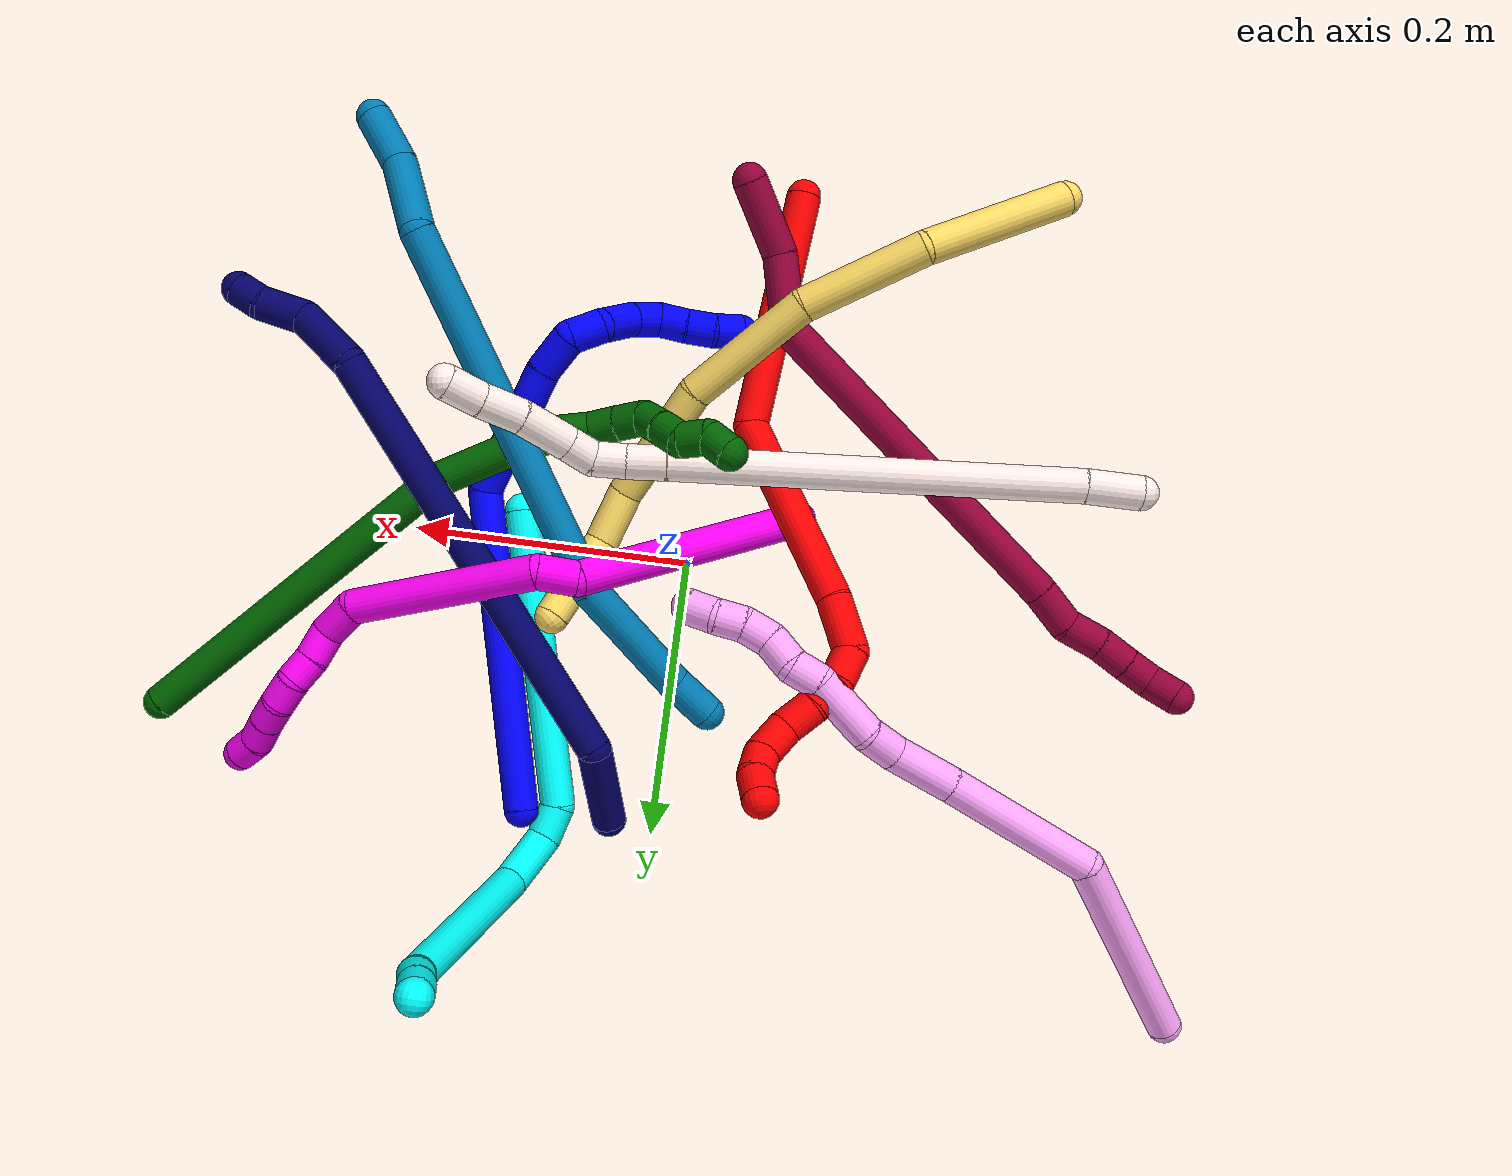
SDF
<sdf version="1.7">
 <world name="default">
  <plugin name="TubeGeneratorPlugin" filename="libtube_generator_plugin.so"/>
  <model name="photoneo_s_sensor">
   <static>1</static>
   <pose>0 0 2 1.57079 1.57079 3.14159</pose>
   <link name="link">
    <inertial><mass>0.1</mass></inertial>
    <sensor name="sensor" type="depth">
     <update_rate>30</update_rate>
     <camera>
      <horizontal_fov>1.22</horizontal_fov>
      <image><width>1920</width><height>1200</height><format>B8G8R8</format></image>
      <clip><near>0.1</near><far>4</far></clip>
      <depth_camera><output>points</output></depth_camera>
     </camera>
     <plugin name="camera_plugin" filename="libgazebo_ros_depth_camera.so">
      <baseline>0.2</baseline>
      <alwaysOn>1</alwaysOn>
      <updateRate>0.0</updateRate>
      <cameraName>camera_ir</cameraName>
      <imageTopicName>/camera/color/image_raw</imageTopicName>
      <cameraInfoTopicName>/camera/color/camera_info</cameraInfoTopicName>
      <depthImageTopicName>/camera/depth/image_raw</depthImageTopicName>
      <depthImageCameraInfoTopicName>/camera/depth/camera_info</depthImageCameraInfoTopicName>
      <pointCloudTopicName>/camera/depth/points</pointCloudTopicName>
      <frameName>fr_optical</frameName>
      <pointCloudCutoff>0.1</pointCloudCutoff>
      <pointCloudCutoffMax>2.0</pointCloudCutoffMax>
      <distortionK1>0</distortionK1>
      <distortionK2>0</distortionK2>
      <distortionK3>0</distortionK3>
      <distortionT1>0</distortionT1>
      <distortionT2>0</distortionT2>
      <CxPrime>0</CxPrime>
      <Cx>0</Cx>
      <Cy>0</Cy>
      <focalLength>0</focalLength>
      <hackBaseline>0</hackBaseline>
     </plugin>
    </sensor>
   </link>
  </model>
  <gravity>0 0 -9.8</gravity>
  <magnetic_field>6e-06 2.3e-05 -4.2e-05</magnetic_field>
  <atmosphere type="adiabatic"/>
  <physics name="default_physics" default="0" type="ode">
   <max_step_size>0.003</max_step_size>
   <real_time_factor>1</real_time_factor>
   <real_time_update_rate>1000</real_time_update_rate>
   <max_contacts>10000</max_contacts>
   <ode>
    <solver>
     <type>quick</type>
     <iters>100</iters>
     <sor>1.3</sor>
     <use_dynamic_moi_rescaling>0</use_dynamic_moi_rescaling>
    </solver>
    <constraints>
     <contact_max_correcting_vel>0</contact_max_correcting_vel>
     <contact_surface_layer>0.001</contact_surface_layer>
     <cfm>0</cfm>
     <erp>0.2</erp>
    </constraints>
   </ode>
  </physics>
  <scene><ambient>0.4 0.4 0.4 1</ambient><background>0.7 0.7 0.7 1</background><shadows>0</shadows></scene>
  <audio><device>default</device></audio>
  <spherical_coordinates>
   <surface_model>EARTH_WGS84</surface_model>
   <latitude_deg>0</latitude_deg>
   <longitude_deg>0</longitude_deg>
   <elevation>0</elevation>
   <heading_deg>0</heading_deg>
  </spherical_coordinates>
  <model name="bin">
   <static>1</static>
   <link name="bottom">
    <collision name="collision-bottom">
     <pose>0 0 -0.01 0 -0 0</pose>
     <geometry><box><size>0.8 0.6 0.02</size></box></geometry>
     <surface>
      <friction><ode><mu>100</mu><mu2>100</mu2></ode></friction>
      <contact><collide_bitmask>65535</collide_bitmask></contact>
     </surface>
    </collision>
   </link>
   <link name="west_wall">
    <collision name="collision-west_wall">
     <pose>-0.41 0 0.1 0 -0 0</pose>
     <geometry><box><size>0.02 0.6 0.2</size></box></geometry>
     <surface>
      <friction><ode><mu>100</mu><mu2>100</mu2></ode></friction>
      <contact><collide_bitmask>65535</collide_bitmask></contact>
     </surface>
    </collision>
   </link>
   <link name="east_wall">
    <collision name="collision-east_wall">
     <pose>0.41 0 0.1 0 -0 0</pose>
     <geometry><box><size>0.02 0.6 0.2</size></box></geometry>
     <surface>
      <friction><ode><mu>100</mu><mu2>100</mu2></ode></friction>
      <contact><collide_bitmask>65535</collide_bitmask></contact>
     </surface>
    </collision>
   </link>
   <link name="south_wall">
    <collision name="collision-south_wall">
     <pose>0 -0.31 0.1 0 -0 0</pose>
     <geometry><box><size>0.8 0.02 0.2</size></box></geometry>
     <surface>
      <friction><ode><mu>100</mu><mu2>100</mu2></ode></friction>
      <contact><collide_bitmask>65535</collide_bitmask></contact>
     </surface>
    </collision>
   </link>
   <link name="north_wall">
    <collision name="collision-north_wall">
     <pose>0 0.31 0.1 0 -0 0</pose>
     <geometry><box><size>0.8 0.02 0.2</size></box></geometry>
     <surface>
      <friction><ode><mu>100</mu><mu2>100</mu2></ode></friction>
      <contact><collide_bitmask>65535</collide_bitmask></contact>
     </surface>
    </collision>
   </link>
  </model>
  <model name="1">
   <static>0</static>
   <link name="1">
    <collision name="collision-cylinder-e_1_1_4">
     <pose>-0.005536 -0.092034 0.071286 0.91176 -0.047517 -0.023302</pose>
     <geometry><cylinder><radius>0.0125</radius><length>0.233088</length></cylinder></geometry>
     <surface>
      <friction><ode><mu>1.16</mu><mu2>1.16</mu2><slip1>0</slip1><slip2>0</slip2></ode></friction>
      <contact><ode><kp>1e+06</kp><kd>1</kd><max_vel>0</max_vel><min_depth>0.001</min_depth></ode></contact>
     </surface>
    </collision>
    <visual name="visual-cylinder-e_1_1_4">
     <pose>-0.005536 -0.092034 0.071286 0.91176 -0.047517 -0.023302</pose>
     <geometry><cylinder><radius>0.0125</radius><length>0.233088</length></cylinder></geometry>
     <material><ambient>0 0 1 1</ambient></material>
    </visual>
    <collision name="collision-cylinder-e_2_4_5">
     <pose>-0.043779 -0.209725 0.16983 0.755148 -0.718108 -0.295538</pose>
     <geometry><cylinder><radius>0.0125</radius><length>0.099422</length></cylinder></geometry>
     <surface>
      <friction><ode><mu>1.16</mu><mu2>1.16</mu2><slip1>0</slip1><slip2>0</slip2></ode></friction>
      <contact><ode><kp>1e+06</kp><kd>1</kd><max_vel>0</max_vel><min_depth>0.001</min_depth></ode></contact>
     </surface>
    </collision>
    <visual name="visual-cylinder-e_2_4_5">
     <pose>-0.043779 -0.209725 0.16983 0.755148 -0.718108 -0.295538</pose>
     <geometry><cylinder><radius>0.0125</radius><length>0.099422</length></cylinder></geometry>
     <material><ambient>0 0 1 1</ambient></material>
    </visual>
    <collision name="collision-cylinder-e_3_5_6">
     <pose>-0.088891 -0.241461 0.203828 0.733916 -0.939164 -0.38525</pose>
     <geometry><cylinder><radius>0.0125</radius><length>0.030738</length></cylinder></geometry>
     <surface>
      <friction><ode><mu>1.16</mu><mu2>1.16</mu2><slip1>0</slip1><slip2>0</slip2></ode></friction>
      <contact><ode><kp>1e+06</kp><kd>1</kd><max_vel>0</max_vel><min_depth>0.001</min_depth></ode></contact>
     </surface>
    </collision>
    <visual name="visual-cylinder-e_3_5_6">
     <pose>-0.088891 -0.241461 0.203828 0.733916 -0.939164 -0.38525</pose>
     <geometry><cylinder><radius>0.0125</radius><length>0.030738</length></cylinder></geometry>
     <material><ambient>0 0 1 1</ambient></material>
    </visual>
    <collision name="collision-cylinder-e_4_6_7">
     <pose>-0.111715 -0.253522 0.207202 2.08302 -0.988316 -1.48858</pose>
     <geometry><cylinder><radius>0.0125</radius><length>0.024956</length></cylinder></geometry>
     <surface>
      <friction><ode><mu>1.16</mu><mu2>1.16</mu2><slip1>0</slip1><slip2>0</slip2></ode></friction>
      <contact><ode><kp>1e+06</kp><kd>1</kd><max_vel>0</max_vel><min_depth>0.001</min_depth></ode></contact>
     </surface>
    </collision>
    <visual name="visual-cylinder-e_4_6_7">
     <pose>-0.111715 -0.253522 0.207202 2.08302 -0.988316 -1.48858</pose>
     <geometry><cylinder><radius>0.0125</radius><length>0.024956</length></cylinder></geometry>
     <material><ambient>0 0 1 1</ambient></material>
    </visual>
    <collision name="collision-cylinder-e_5_7_8">
     <pose>-0.128836 -0.26995 0.194718 2.28855 -0.450184 -0.93349</pose>
     <geometry><cylinder><radius>0.0125</radius><length>0.0308</length></cylinder></geometry>
     <surface>
      <friction><ode><mu>1.16</mu><mu2>1.16</mu2><slip1>0</slip1><slip2>0</slip2></ode></friction>
      <contact><ode><kp>1e+06</kp><kd>1</kd><max_vel>0</max_vel><min_depth>0.001</min_depth></ode></contact>
     </surface>
    </collision>
    <visual name="visual-cylinder-e_5_7_8">
     <pose>-0.128836 -0.26995 0.194718 2.28855 -0.450184 -0.93349</pose>
     <geometry><cylinder><radius>0.0125</radius><length>0.0308</length></cylinder></geometry>
     <material><ambient>0 0 1 1</ambient></material>
    </visual>
    <collision name="collision-cylinder-e_6_8_9">
     <pose>-0.143305 -0.283576 0.179953 2.62856 -0.875485 -2.11997</pose>
     <geometry><cylinder><radius>0.0125</radius><length>0.020232</length></cylinder></geometry>
     <surface>
      <friction><ode><mu>1.16</mu><mu2>1.16</mu2><slip1>0</slip1><slip2>0</slip2></ode></friction>
      <contact><ode><kp>1e+06</kp><kd>1</kd><max_vel>0</max_vel><min_depth>0.001</min_depth></ode></contact>
     </surface>
    </collision>
    <visual name="visual-cylinder-e_6_8_9">
     <pose>-0.143305 -0.283576 0.179953 2.62856 -0.875485 -2.11997</pose>
     <geometry><cylinder><radius>0.0125</radius><length>0.020232</length></cylinder></geometry>
     <material><ambient>0 0 1 1</ambient></material>
    </visual>
    <collision name="collision-cylinder-e_7_9_10">
     <pose>-0.159803 -0.285874 0.169155 -2.97201 -1.03134 2.84391</pose>
     <geometry><cylinder><radius>0.0125</radius><length>0.020349</length></cylinder></geometry>
     <surface>
      <friction><ode><mu>1.16</mu><mu2>1.16</mu2><slip1>0</slip1><slip2>0</slip2></ode></friction>
      <contact><ode><kp>1e+06</kp><kd>1</kd><max_vel>0</max_vel><min_depth>0.001</min_depth></ode></contact>
     </surface>
    </collision>
    <visual name="visual-cylinder-e_7_9_10">
     <pose>-0.159803 -0.285874 0.169155 -2.97201 -1.03134 2.84391</pose>
     <geometry><cylinder><radius>0.0125</radius><length>0.020349</length></cylinder></geometry>
     <material><ambient>0 0 1 1</ambient></material>
    </visual>
    <collision name="collision-cylinder-e_8_10_11">
     <pose>-0.177141 -0.285196 0.158676 3.10343 -1.01632 -3.0731</pose>
     <geometry><cylinder><radius>0.0125</radius><length>0.020252</length></cylinder></geometry>
     <surface>
      <friction><ode><mu>1.16</mu><mu2>1.16</mu2><slip1>0</slip1><slip2>0</slip2></ode></friction>
      <contact><ode><kp>1e+06</kp><kd>1</kd><max_vel>0</max_vel><min_depth>0.001</min_depth></ode></contact>
     </surface>
    </collision>
    <visual name="visual-cylinder-e_8_10_11">
     <pose>-0.177141 -0.285196 0.158676 3.10343 -1.01632 -3.0731</pose>
     <geometry><cylinder><radius>0.0125</radius><length>0.020252</length></cylinder></geometry>
     <material><ambient>0 0 1 1</ambient></material>
    </visual>
    <collision name="collision-cylinder-e_9_11_2">
     <pose>-0.193774 -0.287934 0.147797 2.71328 -0.920543 -2.31479</pose>
     <geometry><cylinder><radius>0.0125</radius><length>0.020163</length></cylinder></geometry>
     <surface>
      <friction><ode><mu>1.16</mu><mu2>1.16</mu2><slip1>0</slip1><slip2>0</slip2></ode></friction>
      <contact><ode><kp>1e+06</kp><kd>1</kd><max_vel>0</max_vel><min_depth>0.001</min_depth></ode></contact>
     </surface>
    </collision>
    <visual name="visual-cylinder-e_9_11_2">
     <pose>-0.193774 -0.287934 0.147797 2.71328 -0.920543 -2.31479</pose>
     <geometry><cylinder><radius>0.0125</radius><length>0.020163</length></cylinder></geometry>
     <material><ambient>0 0 1 1</ambient></material>
    </visual>
    <collision name="collision-sphere-2">
     <pose>-0.201799 -0.290469 0.142245 0 -0 0</pose>
     <geometry><sphere><radius>0.0125</radius></sphere></geometry>
     <surface>
      <friction><ode><mu>1.16</mu><mu2>1.16</mu2><slip1>0</slip1><slip2>0</slip2></ode></friction>
      <contact><ode><kp>1e+06</kp><kd>1</kd><max_vel>0</max_vel><min_depth>0.001</min_depth></ode></contact>
     </surface>
    </collision>
    <visual name="visual-sphere-2">
     <pose>-0.201799 -0.290469 0.142245 0 -0 0</pose>
     <geometry><sphere><radius>0.0125</radius></sphere></geometry>
     <material><ambient>0 0 1 1</ambient></material>
    </visual>
    <collision name="collision-sphere-11">
     <pose>-0.18575 -0.285399 0.153349 0 -0 0</pose>
     <geometry><sphere><radius>0.0125</radius></sphere></geometry>
     <surface>
      <friction><ode><mu>1.16</mu><mu2>1.16</mu2><slip1>0</slip1><slip2>0</slip2></ode></friction>
      <contact><ode><kp>1e+06</kp><kd>1</kd><max_vel>0</max_vel><min_depth>0.001</min_depth></ode></contact>
     </surface>
    </collision>
    <visual name="visual-sphere-11">
     <pose>-0.18575 -0.285399 0.153349 0 -0 0</pose>
     <geometry><sphere><radius>0.0125</radius></sphere></geometry>
     <material><ambient>0 0 1 1</ambient></material>
    </visual>
    <collision name="collision-sphere-10">
     <pose>-0.168532 -0.284992 0.164004 0 -0 0</pose>
     <geometry><sphere><radius>0.0125</radius></sphere></geometry>
     <surface>
      <friction><ode><mu>1.16</mu><mu2>1.16</mu2><slip1>0</slip1><slip2>0</slip2></ode></friction>
      <contact><ode><kp>1e+06</kp><kd>1</kd><max_vel>0</max_vel><min_depth>0.001</min_depth></ode></contact>
     </surface>
    </collision>
    <visual name="visual-sphere-10">
     <pose>-0.168532 -0.284992 0.164004 0 -0 0</pose>
     <geometry><sphere><radius>0.0125</radius></sphere></geometry>
     <material><ambient>0 0 1 1</ambient></material>
    </visual>
    <collision name="collision-sphere-9">
     <pose>-0.151073 -0.286757 0.174306 0 -0 0</pose>
     <geometry><sphere><radius>0.0125</radius></sphere></geometry>
     <surface>
      <friction><ode><mu>1.16</mu><mu2>1.16</mu2><slip1>0</slip1><slip2>0</slip2></ode></friction>
      <contact><ode><kp>1e+06</kp><kd>1</kd><max_vel>0</max_vel><min_depth>0.001</min_depth></ode></contact>
     </surface>
    </collision>
    <visual name="visual-sphere-9">
     <pose>-0.151073 -0.286757 0.174306 0 -0 0</pose>
     <geometry><sphere><radius>0.0125</radius></sphere></geometry>
     <material><ambient>0 0 1 1</ambient></material>
    </visual>
    <collision name="collision-sphere-4">
     <pose>-0.011071 -0.184067 0.142571 0 -0 0</pose>
     <geometry><sphere><radius>0.0125</radius></sphere></geometry>
     <surface>
      <friction><ode><mu>1.16</mu><mu2>1.16</mu2><slip1>0</slip1><slip2>0</slip2></ode></friction>
      <contact><ode><kp>1e+06</kp><kd>1</kd><max_vel>0</max_vel><min_depth>0.001</min_depth></ode></contact>
     </surface>
    </collision>
    <visual name="visual-sphere-4">
     <pose>-0.011071 -0.184067 0.142571 0 -0 0</pose>
     <geometry><sphere><radius>0.0125</radius></sphere></geometry>
     <material><ambient>0 0 1 1</ambient></material>
    </visual>
    <collision name="collision-sphere-1">
     <geometry><sphere><radius>0.0125</radius></sphere></geometry>
     <surface>
      <friction><ode><mu>1.16</mu><mu2>1.16</mu2><slip1>0</slip1><slip2>0</slip2></ode></friction>
      <contact><ode><kp>1e+06</kp><kd>1</kd><max_vel>0</max_vel><min_depth>0.001</min_depth></ode></contact>
     </surface>
    </collision>
    <visual name="visual-sphere-1">
     <geometry><sphere><radius>0.0125</radius></sphere></geometry>
     <material><ambient>0 0 1 1</ambient></material>
    </visual>
    <collision name="collision-sphere-8">
     <pose>-0.135538 -0.280395 0.185599 0 -0 0</pose>
     <geometry><sphere><radius>0.0125</radius></sphere></geometry>
     <surface>
      <friction><ode><mu>1.16</mu><mu2>1.16</mu2><slip1>0</slip1><slip2>0</slip2></ode></friction>
      <contact><ode><kp>1e+06</kp><kd>1</kd><max_vel>0</max_vel><min_depth>0.001</min_depth></ode></contact>
     </surface>
    </collision>
    <visual name="visual-sphere-8">
     <pose>-0.135538 -0.280395 0.185599 0 -0 0</pose>
     <geometry><sphere><radius>0.0125</radius></sphere></geometry>
     <material><ambient>0 0 1 1</ambient></material>
    </visual>
    <collision name="collision-sphere-5">
     <pose>-0.076487 -0.235382 0.197089 0 -0 0</pose>
     <geometry><sphere><radius>0.0125</radius></sphere></geometry>
     <surface>
      <friction><ode><mu>1.16</mu><mu2>1.16</mu2><slip1>0</slip1><slip2>0</slip2></ode></friction>
      <contact><ode><kp>1e+06</kp><kd>1</kd><max_vel>0</max_vel><min_depth>0.001</min_depth></ode></contact>
     </surface>
    </collision>
    <visual name="visual-sphere-5">
     <pose>-0.076487 -0.235382 0.197089 0 -0 0</pose>
     <geometry><sphere><radius>0.0125</radius></sphere></geometry>
     <material><ambient>0 0 1 1</ambient></material>
    </visual>
    <collision name="collision-sphere-6">
     <pose>-0.101294 -0.247539 0.210566 0 -0 0</pose>
     <geometry><sphere><radius>0.0125</radius></sphere></geometry>
     <surface>
      <friction><ode><mu>1.16</mu><mu2>1.16</mu2><slip1>0</slip1><slip2>0</slip2></ode></friction>
      <contact><ode><kp>1e+06</kp><kd>1</kd><max_vel>0</max_vel><min_depth>0.001</min_depth></ode></contact>
     </surface>
    </collision>
    <visual name="visual-sphere-6">
     <pose>-0.101294 -0.247539 0.210566 0 -0 0</pose>
     <geometry><sphere><radius>0.0125</radius></sphere></geometry>
     <material><ambient>0 0 1 1</ambient></material>
    </visual>
    <collision name="collision-sphere-7">
     <pose>-0.122135 -0.259505 0.203838 0 -0 0</pose>
     <geometry><sphere><radius>0.0125</radius></sphere></geometry>
     <surface>
      <friction><ode><mu>1.16</mu><mu2>1.16</mu2><slip1>0</slip1><slip2>0</slip2></ode></friction>
      <contact><ode><kp>1e+06</kp><kd>1</kd><max_vel>0</max_vel><min_depth>0.001</min_depth></ode></contact>
     </surface>
    </collision>
    <visual name="visual-sphere-7">
     <pose>-0.122135 -0.259505 0.203838 0 -0 0</pose>
     <geometry><sphere><radius>0.0125</radius></sphere></geometry>
     <material><ambient>0 0 1 1</ambient></material>
    </visual>
    <inertial>
     <pose>-0.057554 -0.175005 0.128421 0 -0 0</pose>
     <mass>0.5</mass>
     <inertia>
      <ixx>0.001061</ixx>
      <ixy>0</ixy>
      <ixz>0</ixz>
      <iyy>0.000661</iyy>
      <iyz>0</iyz>
      <izz>0.00102</izz>
     </inertia>
    </inertial>
   </link>
   <pose>0.095368 0.191956 0.0221 0.72177 0.353064 0.313822</pose>
  </model>
  <model name="2">
   <static>0</static>
   <link name="2">
    <collision name="collision-cylinder-e_1_1_4">
     <pose>0.028869 0.027358 0.077668 -0.338674 0.337193 -0.058188</pose>
     <geometry><cylinder><radius>0.0125</radius><length>0.174518</length></cylinder></geometry>
     <surface>
      <friction><ode><mu>1.16</mu><mu2>1.16</mu2><slip1>0</slip1><slip2>0</slip2></ode></friction>
      <contact><ode><kp>1e+06</kp><kd>1</kd><max_vel>0</max_vel><min_depth>0.001</min_depth></ode></contact>
     </surface>
    </collision>
    <visual name="visual-cylinder-e_1_1_4">
     <pose>0.028869 0.027358 0.077668 -0.338674 0.337193 -0.058188</pose>
     <geometry><cylinder><radius>0.0125</radius><length>0.174518</length></cylinder></geometry>
     <material><ambient>1 0 0 1</ambient></material>
    </visual>
    <collision name="collision-cylinder-e_2_4_5">
     <pose>0.038917 0.054653 0.226309 0.000888 -0.259213 -0.000116</pose>
     <geometry><cylinder><radius>0.0125</radius><length>0.146853</length></cylinder></geometry>
     <surface>
      <friction><ode><mu>1.16</mu><mu2>1.16</mu2><slip1>0</slip1><slip2>0</slip2></ode></friction>
      <contact><ode><kp>1e+06</kp><kd>1</kd><max_vel>0</max_vel><min_depth>0.001</min_depth></ode></contact>
     </surface>
    </collision>
    <visual name="visual-cylinder-e_2_4_5">
     <pose>0.038917 0.054653 0.226309 0.000888 -0.259213 -0.000116</pose>
     <geometry><cylinder><radius>0.0125</radius><length>0.146853</length></cylinder></geometry>
     <material><ambient>1 0 0 1</ambient></material>
    </visual>
    <collision name="collision-cylinder-e_3_5_6">
     <pose>0.017045 0.056807 0.316459 -0.115073 -0.156733 0.009046</pose>
     <geometry><cylinder><radius>0.0125</radius><length>0.03909</length></cylinder></geometry>
     <surface>
      <friction><ode><mu>1.16</mu><mu2>1.16</mu2><slip1>0</slip1><slip2>0</slip2></ode></friction>
      <contact><ode><kp>1e+06</kp><kd>1</kd><max_vel>0</max_vel><min_depth>0.001</min_depth></ode></contact>
     </surface>
    </collision>
    <visual name="visual-cylinder-e_3_5_6">
     <pose>0.017045 0.056807 0.316459 -0.115073 -0.156733 0.009046</pose>
     <geometry><cylinder><radius>0.0125</radius><length>0.03909</length></cylinder></geometry>
     <material><ambient>1 0 0 1</ambient></material>
    </visual>
    <collision name="collision-cylinder-e_4_6_7">
     <pose>0.020549 0.05922 0.345852 -0.019222 0.570369 -0.005636</pose>
     <geometry><cylinder><radius>0.0125</radius><length>0.024276</length></cylinder></geometry>
     <surface>
      <friction><ode><mu>1.16</mu><mu2>1.16</mu2><slip1>0</slip1><slip2>0</slip2></ode></friction>
      <contact><ode><kp>1e+06</kp><kd>1</kd><max_vel>0</max_vel><min_depth>0.001</min_depth></ode></contact>
     </surface>
    </collision>
    <visual name="visual-cylinder-e_4_6_7">
     <pose>0.020549 0.05922 0.345852 -0.019222 0.570369 -0.005636</pose>
     <geometry><cylinder><radius>0.0125</radius><length>0.024276</length></cylinder></geometry>
     <material><ambient>1 0 0 1</ambient></material>
    </visual>
    <collision name="collision-cylinder-e_5_7_8">
     <pose>0.036201 0.060372 0.36348 -0.12818 0.883091 -0.060651</pose>
     <geometry><cylinder><radius>0.0125</radius><length>0.023549</length></cylinder></geometry>
     <surface>
      <friction><ode><mu>1.16</mu><mu2>1.16</mu2><slip1>0</slip1><slip2>0</slip2></ode></friction>
      <contact><ode><kp>1e+06</kp><kd>1</kd><max_vel>0</max_vel><min_depth>0.001</min_depth></ode></contact>
     </surface>
    </collision>
    <visual name="visual-cylinder-e_5_7_8">
     <pose>0.036201 0.060372 0.36348 -0.12818 0.883091 -0.060651</pose>
     <geometry><cylinder><radius>0.0125</radius><length>0.023549</length></cylinder></geometry>
     <material><ambient>1 0 0 1</ambient></material>
    </visual>
    <collision name="collision-cylinder-e_6_8_9">
     <pose>0.055609 0.063396 0.376724 -0.340859 1.03025 -0.19424</pose>
     <geometry><cylinder><radius>0.0125</radius><length>0.024048</length></cylinder></geometry>
     <surface>
      <friction><ode><mu>1.16</mu><mu2>1.16</mu2><slip1>0</slip1><slip2>0</slip2></ode></friction>
      <contact><ode><kp>1e+06</kp><kd>1</kd><max_vel>0</max_vel><min_depth>0.001</min_depth></ode></contact>
     </surface>
    </collision>
    <visual name="visual-cylinder-e_6_8_9">
     <pose>0.055609 0.063396 0.376724 -0.340859 1.03025 -0.19424</pose>
     <geometry><cylinder><radius>0.0125</radius><length>0.024048</length></cylinder></geometry>
     <material><ambient>1 0 0 1</ambient></material>
    </visual>
    <collision name="collision-cylinder-e_7_9_10">
     <pose>0.075097 0.06404 0.391397 0.159668 0.797687 0.067407</pose>
     <geometry><cylinder><radius>0.0125</radius><length>0.025647</length></cylinder></geometry>
     <surface>
      <friction><ode><mu>1.16</mu><mu2>1.16</mu2><slip1>0</slip1><slip2>0</slip2></ode></friction>
      <contact><ode><kp>1e+06</kp><kd>1</kd><max_vel>0</max_vel><min_depth>0.001</min_depth></ode></contact>
     </surface>
    </collision>
    <visual name="visual-cylinder-e_7_9_10">
     <pose>0.075097 0.06404 0.391397 0.159668 0.797687 0.067407</pose>
     <geometry><cylinder><radius>0.0125</radius><length>0.025647</length></cylinder></geometry>
     <material><ambient>1 0 0 1</ambient></material>
    </visual>
    <collision name="collision-cylinder-e_8_10_11">
     <pose>0.087907 0.058165 0.409069 0.466917 0.351978 0.084523</pose>
     <geometry><cylinder><radius>0.0125</radius><length>0.02107</length></cylinder></geometry>
     <surface>
      <friction><ode><mu>1.16</mu><mu2>1.16</mu2><slip1>0</slip1><slip2>0</slip2></ode></friction>
      <contact><ode><kp>1e+06</kp><kd>1</kd><max_vel>0</max_vel><min_depth>0.001</min_depth></ode></contact>
     </surface>
    </collision>
    <visual name="visual-cylinder-e_8_10_11">
     <pose>0.087907 0.058165 0.409069 0.466917 0.351978 0.084523</pose>
     <geometry><cylinder><radius>0.0125</radius><length>0.02107</length></cylinder></geometry>
     <material><ambient>1 0 0 1</ambient></material>
    </visual>
    <collision name="collision-cylinder-e_9_11_2">
     <pose>0.09148 0.049446 0.427465 0.419617 -0.005661 -0.001206</pose>
     <geometry><cylinder><radius>0.0125</radius><length>0.020949</length></cylinder></geometry>
     <surface>
      <friction><ode><mu>1.16</mu><mu2>1.16</mu2><slip1>0</slip1><slip2>0</slip2></ode></friction>
      <contact><ode><kp>1e+06</kp><kd>1</kd><max_vel>0</max_vel><min_depth>0.001</min_depth></ode></contact>
     </surface>
    </collision>
    <visual name="visual-cylinder-e_9_11_2">
     <pose>0.09148 0.049446 0.427465 0.419617 -0.005661 -0.001206</pose>
     <geometry><cylinder><radius>0.0125</radius><length>0.020949</length></cylinder></geometry>
     <material><ambient>1 0 0 1</ambient></material>
    </visual>
    <collision name="collision-sphere-2">
     <pose>0.09142 0.045179 0.437031 0 -0 0</pose>
     <geometry><sphere><radius>0.0125</radius></sphere></geometry>
     <surface>
      <friction><ode><mu>1.16</mu><mu2>1.16</mu2><slip1>0</slip1><slip2>0</slip2></ode></friction>
      <contact><ode><kp>1e+06</kp><kd>1</kd><max_vel>0</max_vel><min_depth>0.001</min_depth></ode></contact>
     </surface>
    </collision>
    <visual name="visual-sphere-2">
     <pose>0.09142 0.045179 0.437031 0 -0 0</pose>
     <geometry><sphere><radius>0.0125</radius></sphere></geometry>
     <material><ambient>1 0 0 1</ambient></material>
    </visual>
    <collision name="collision-sphere-11">
     <pose>0.091539 0.053714 0.4179 0 -0 0</pose>
     <geometry><sphere><radius>0.0125</radius></sphere></geometry>
     <surface>
      <friction><ode><mu>1.16</mu><mu2>1.16</mu2><slip1>0</slip1><slip2>0</slip2></ode></friction>
      <contact><ode><kp>1e+06</kp><kd>1</kd><max_vel>0</max_vel><min_depth>0.001</min_depth></ode></contact>
     </surface>
    </collision>
    <visual name="visual-sphere-11">
     <pose>0.091539 0.053714 0.4179 0 -0 0</pose>
     <geometry><sphere><radius>0.0125</radius></sphere></geometry>
     <material><ambient>1 0 0 1</ambient></material>
    </visual>
    <collision name="collision-sphere-10">
     <pose>0.084275 0.062616 0.400239 0 -0 0</pose>
     <geometry><sphere><radius>0.0125</radius></sphere></geometry>
     <surface>
      <friction><ode><mu>1.16</mu><mu2>1.16</mu2><slip1>0</slip1><slip2>0</slip2></ode></friction>
      <contact><ode><kp>1e+06</kp><kd>1</kd><max_vel>0</max_vel><min_depth>0.001</min_depth></ode></contact>
     </surface>
    </collision>
    <visual name="visual-sphere-10">
     <pose>0.084275 0.062616 0.400239 0 -0 0</pose>
     <geometry><sphere><radius>0.0125</radius></sphere></geometry>
     <material><ambient>1 0 0 1</ambient></material>
    </visual>
    <collision name="collision-sphere-9">
     <pose>0.065919 0.065464 0.382556 0 -0 0</pose>
     <geometry><sphere><radius>0.0125</radius></sphere></geometry>
     <surface>
      <friction><ode><mu>1.16</mu><mu2>1.16</mu2><slip1>0</slip1><slip2>0</slip2></ode></friction>
      <contact><ode><kp>1e+06</kp><kd>1</kd><max_vel>0</max_vel><min_depth>0.001</min_depth></ode></contact>
     </surface>
    </collision>
    <visual name="visual-sphere-9">
     <pose>0.065919 0.065464 0.382556 0 -0 0</pose>
     <geometry><sphere><radius>0.0125</radius></sphere></geometry>
     <material><ambient>1 0 0 1</ambient></material>
    </visual>
    <collision name="collision-sphere-4">
     <pose>0.057737 0.054716 0.155335 0 -0 0</pose>
     <geometry><sphere><radius>0.0125</radius></sphere></geometry>
     <surface>
      <friction><ode><mu>1.16</mu><mu2>1.16</mu2><slip1>0</slip1><slip2>0</slip2></ode></friction>
      <contact><ode><kp>1e+06</kp><kd>1</kd><max_vel>0</max_vel><min_depth>0.001</min_depth></ode></contact>
     </surface>
    </collision>
    <visual name="visual-sphere-4">
     <pose>0.057737 0.054716 0.155335 0 -0 0</pose>
     <geometry><sphere><radius>0.0125</radius></sphere></geometry>
     <material><ambient>1 0 0 1</ambient></material>
    </visual>
    <collision name="collision-sphere-1">
     <geometry><sphere><radius>0.0125</radius></sphere></geometry>
     <surface>
      <friction><ode><mu>1.16</mu><mu2>1.16</mu2><slip1>0</slip1><slip2>0</slip2></ode></friction>
      <contact><ode><kp>1e+06</kp><kd>1</kd><max_vel>0</max_vel><min_depth>0.001</min_depth></ode></contact>
     </surface>
    </collision>
    <visual name="visual-sphere-1">
     <geometry><sphere><radius>0.0125</radius></sphere></geometry>
     <material><ambient>1 0 0 1</ambient></material>
    </visual>
    <collision name="collision-sphere-8">
     <pose>0.045299 0.061327 0.370892 0 -0 0</pose>
     <geometry><sphere><radius>0.0125</radius></sphere></geometry>
     <surface>
      <friction><ode><mu>1.16</mu><mu2>1.16</mu2><slip1>0</slip1><slip2>0</slip2></ode></friction>
      <contact><ode><kp>1e+06</kp><kd>1</kd><max_vel>0</max_vel><min_depth>0.001</min_depth></ode></contact>
     </surface>
    </collision>
    <visual name="visual-sphere-8">
     <pose>0.045299 0.061327 0.370892 0 -0 0</pose>
     <geometry><sphere><radius>0.0125</radius></sphere></geometry>
     <material><ambient>1 0 0 1</ambient></material>
    </visual>
    <collision name="collision-sphere-5">
     <pose>0.020096 0.05459 0.297282 0 -0 0</pose>
     <geometry><sphere><radius>0.0125</radius></sphere></geometry>
     <surface>
      <friction><ode><mu>1.16</mu><mu2>1.16</mu2><slip1>0</slip1><slip2>0</slip2></ode></friction>
      <contact><ode><kp>1e+06</kp><kd>1</kd><max_vel>0</max_vel><min_depth>0.001</min_depth></ode></contact>
     </surface>
    </collision>
    <visual name="visual-sphere-5">
     <pose>0.020096 0.05459 0.297282 0 -0 0</pose>
     <geometry><sphere><radius>0.0125</radius></sphere></geometry>
     <material><ambient>1 0 0 1</ambient></material>
    </visual>
    <collision name="collision-sphere-6">
     <pose>0.013995 0.059023 0.335637 0 -0 0</pose>
     <geometry><sphere><radius>0.0125</radius></sphere></geometry>
     <surface>
      <friction><ode><mu>1.16</mu><mu2>1.16</mu2><slip1>0</slip1><slip2>0</slip2></ode></friction>
      <contact><ode><kp>1e+06</kp><kd>1</kd><max_vel>0</max_vel><min_depth>0.001</min_depth></ode></contact>
     </surface>
    </collision>
    <visual name="visual-sphere-6">
     <pose>0.013995 0.059023 0.335637 0 -0 0</pose>
     <geometry><sphere><radius>0.0125</radius></sphere></geometry>
     <material><ambient>1 0 0 1</ambient></material>
    </visual>
    <collision name="collision-sphere-7">
     <pose>0.027102 0.059416 0.356067 0 -0 0</pose>
     <geometry><sphere><radius>0.0125</radius></sphere></geometry>
     <surface>
      <friction><ode><mu>1.16</mu><mu2>1.16</mu2><slip1>0</slip1><slip2>0</slip2></ode></friction>
      <contact><ode><kp>1e+06</kp><kd>1</kd><max_vel>0</max_vel><min_depth>0.001</min_depth></ode></contact>
     </surface>
    </collision>
    <visual name="visual-sphere-7">
     <pose>0.027102 0.059416 0.356067 0 -0 0</pose>
     <geometry><sphere><radius>0.0125</radius></sphere></geometry>
     <material><ambient>1 0 0 1</ambient></material>
    </visual>
    <inertial>
     <pose>0.039605 0.046617 0.225572 0 -0 0</pose>
     <mass>0.5</mass>
     <inertia>
      <ixx>0.000682</ixx>
      <ixy>0</ixy>
      <ixz>0</ixz>
      <iyy>0.000693</iyy>
      <iyz>0</iyz>
      <izz>-0.000192</izz>
     </inertia>
    </inertial>
   </link>
   <pose>-0.049353 -0.275858 0.011091 -1.12666 -0.06479 0.233169</pose>
  </model>
  <model name="3">
   <static>0</static>
   <link name="3">
    <collision name="collision-cylinder-e_1_1_4">
     <pose>0.020358 0.022303 0.103838 -0.211576 0.18939 -0.02017</pose>
     <geometry><cylinder><radius>0.0125</radius><length>0.216279</length></cylinder></geometry>
     <surface>
      <friction><ode><mu>1.16</mu><mu2>1.16</mu2><slip1>0</slip1><slip2>0</slip2></ode></friction>
      <contact><ode><kp>1e+06</kp><kd>1</kd><max_vel>0</max_vel><min_depth>0.001</min_depth></ode></contact>
     </surface>
    </collision>
    <visual name="visual-cylinder-e_1_1_4">
     <pose>0.020358 0.022303 0.103838 -0.211576 0.18939 -0.02017</pose>
     <geometry><cylinder><radius>0.0125</radius><length>0.216279</length></cylinder></geometry>
     <material><ambient>0.003922 1 0.996078 1</ambient></material>
    </visual>
    <collision name="collision-cylinder-e_2_4_5">
     <pose>0.03964 0.041516 0.220125 0.243319 -0.083707 -0.01024</pose>
     <geometry><cylinder><radius>0.0125</radius><length>0.025745</length></cylinder></geometry>
     <surface>
      <friction><ode><mu>1.16</mu><mu2>1.16</mu2><slip1>0</slip1><slip2>0</slip2></ode></friction>
      <contact><ode><kp>1e+06</kp><kd>1</kd><max_vel>0</max_vel><min_depth>0.001</min_depth></ode></contact>
     </surface>
    </collision>
    <visual name="visual-cylinder-e_2_4_5">
     <pose>0.03964 0.041516 0.220125 0.243319 -0.083707 -0.01024</pose>
     <geometry><cylinder><radius>0.0125</radius><length>0.025745</length></cylinder></geometry>
     <material><ambient>0.003922 1 0.996078 1</ambient></material>
    </visual>
    <collision name="collision-cylinder-e_3_5_6">
     <pose>0.02546 0.035316 0.249088 0.18614 -0.662295 -0.06416</pose>
     <geometry><cylinder><radius>0.0125</radius><length>0.042618</length></cylinder></geometry>
     <surface>
      <friction><ode><mu>1.16</mu><mu2>1.16</mu2><slip1>0</slip1><slip2>0</slip2></ode></friction>
      <contact><ode><kp>1e+06</kp><kd>1</kd><max_vel>0</max_vel><min_depth>0.001</min_depth></ode></contact>
     </surface>
    </collision>
    <visual name="visual-cylinder-e_3_5_6">
     <pose>0.02546 0.035316 0.249088 0.18614 -0.662295 -0.06416</pose>
     <geometry><cylinder><radius>0.0125</radius><length>0.042618</length></cylinder></geometry>
     <material><ambient>0.003922 1 0.996078 1</ambient></material>
    </visual>
    <collision name="collision-cylinder-e_4_6_7">
     <pose>-0.055598 0.045478 0.291872 -0.467828 -1.16207 0.310411</pose>
     <geometry><cylinder><radius>0.0125</radius><length>0.148109</length></cylinder></geometry>
     <surface>
      <friction><ode><mu>1.16</mu><mu2>1.16</mu2><slip1>0</slip1><slip2>0</slip2></ode></friction>
      <contact><ode><kp>1e+06</kp><kd>1</kd><max_vel>0</max_vel><min_depth>0.001</min_depth></ode></contact>
     </surface>
    </collision>
    <visual name="visual-cylinder-e_4_6_7">
     <pose>-0.055598 0.045478 0.291872 -0.467828 -1.16207 0.310411</pose>
     <geometry><cylinder><radius>0.0125</radius><length>0.148109</length></cylinder></geometry>
     <material><ambient>0.003922 1 0.996078 1</ambient></material>
    </visual>
    <collision name="collision-cylinder-e_5_7_8">
     <pose>-0.133737 0.065358 0.316663 -1.79097 -0.984138 1.17962</pose>
     <geometry><cylinder><radius>0.0125</radius><length>0.02446</length></cylinder></geometry>
     <surface>
      <friction><ode><mu>1.16</mu><mu2>1.16</mu2><slip1>0</slip1><slip2>0</slip2></ode></friction>
      <contact><ode><kp>1e+06</kp><kd>1</kd><max_vel>0</max_vel><min_depth>0.001</min_depth></ode></contact>
     </surface>
    </collision>
    <visual name="visual-cylinder-e_5_7_8">
     <pose>-0.133737 0.065358 0.316663 -1.79097 -0.984138 1.17962</pose>
     <geometry><cylinder><radius>0.0125</radius><length>0.02446</length></cylinder></geometry>
     <material><ambient>0.003922 1 0.996078 1</ambient></material>
    </visual>
    <collision name="collision-cylinder-e_6_8_9">
     <pose>-0.152183 0.078312 0.316257 -1.40334 -0.90883 0.783096</pose>
     <geometry><cylinder><radius>0.0125</radius><length>0.020945</length></cylinder></geometry>
     <surface>
      <friction><ode><mu>1.16</mu><mu2>1.16</mu2><slip1>0</slip1><slip2>0</slip2></ode></friction>
      <contact><ode><kp>1e+06</kp><kd>1</kd><max_vel>0</max_vel><min_depth>0.001</min_depth></ode></contact>
     </surface>
    </collision>
    <visual name="visual-cylinder-e_6_8_9">
     <pose>-0.152183 0.078312 0.316257 -1.40334 -0.90883 0.783096</pose>
     <geometry><cylinder><radius>0.0125</radius><length>0.020945</length></cylinder></geometry>
     <material><ambient>0.003922 1 0.996078 1</ambient></material>
    </visual>
    <collision name="collision-cylinder-e_7_9_2">
     <pose>-0.169403 0.090667 0.319036 -1.29417 -0.962047 0.751277</pose>
     <geometry><cylinder><radius>0.0125</radius><length>0.021844</length></cylinder></geometry>
     <surface>
      <friction><ode><mu>1.16</mu><mu2>1.16</mu2><slip1>0</slip1><slip2>0</slip2></ode></friction>
      <contact><ode><kp>1e+06</kp><kd>1</kd><max_vel>0</max_vel><min_depth>0.001</min_depth></ode></contact>
     </surface>
    </collision>
    <visual name="visual-cylinder-e_7_9_2">
     <pose>-0.169403 0.090667 0.319036 -1.29417 -0.962047 0.751277</pose>
     <geometry><cylinder><radius>0.0125</radius><length>0.021844</length></cylinder></geometry>
     <material><ambient>0.003922 1 0.996078 1</ambient></material>
    </visual>
    <collision name="collision-sphere-2">
     <pose>-0.178363 0.096675 0.320741 0 -0 0</pose>
     <geometry><sphere><radius>0.0125</radius></sphere></geometry>
     <surface>
      <friction><ode><mu>1.16</mu><mu2>1.16</mu2><slip1>0</slip1><slip2>0</slip2></ode></friction>
      <contact><ode><kp>1e+06</kp><kd>1</kd><max_vel>0</max_vel><min_depth>0.001</min_depth></ode></contact>
     </surface>
    </collision>
    <visual name="visual-sphere-2">
     <pose>-0.178363 0.096675 0.320741 0 -0 0</pose>
     <geometry><sphere><radius>0.0125</radius></sphere></geometry>
     <material><ambient>0.003922 1 0.996078 1</ambient></material>
    </visual>
    <collision name="collision-sphere-9">
     <pose>-0.160444 0.084659 0.31733 0 -0 0</pose>
     <geometry><sphere><radius>0.0125</radius></sphere></geometry>
     <surface>
      <friction><ode><mu>1.16</mu><mu2>1.16</mu2><slip1>0</slip1><slip2>0</slip2></ode></friction>
      <contact><ode><kp>1e+06</kp><kd>1</kd><max_vel>0</max_vel><min_depth>0.001</min_depth></ode></contact>
     </surface>
    </collision>
    <visual name="visual-sphere-9">
     <pose>-0.160444 0.084659 0.31733 0 -0 0</pose>
     <geometry><sphere><radius>0.0125</radius></sphere></geometry>
     <material><ambient>0.003922 1 0.996078 1</ambient></material>
    </visual>
    <collision name="collision-sphere-4">
     <pose>0.040717 0.044607 0.207675 0 -0 0</pose>
     <geometry><sphere><radius>0.0125</radius></sphere></geometry>
     <surface>
      <friction><ode><mu>1.16</mu><mu2>1.16</mu2><slip1>0</slip1><slip2>0</slip2></ode></friction>
      <contact><ode><kp>1e+06</kp><kd>1</kd><max_vel>0</max_vel><min_depth>0.001</min_depth></ode></contact>
     </surface>
    </collision>
    <visual name="visual-sphere-4">
     <pose>0.040717 0.044607 0.207675 0 -0 0</pose>
     <geometry><sphere><radius>0.0125</radius></sphere></geometry>
     <material><ambient>0.003922 1 0.996078 1</ambient></material>
    </visual>
    <collision name="collision-sphere-1">
     <geometry><sphere><radius>0.0125</radius></sphere></geometry>
     <surface>
      <friction><ode><mu>1.16</mu><mu2>1.16</mu2><slip1>0</slip1><slip2>0</slip2></ode></friction>
      <contact><ode><kp>1e+06</kp><kd>1</kd><max_vel>0</max_vel><min_depth>0.001</min_depth></ode></contact>
     </surface>
    </collision>
    <visual name="visual-sphere-1">
     <geometry><sphere><radius>0.0125</radius></sphere></geometry>
     <material><ambient>0.003922 1 0.996078 1</ambient></material>
    </visual>
    <collision name="collision-sphere-8">
     <pose>-0.143923 0.071965 0.315184 0 -0 0</pose>
     <geometry><sphere><radius>0.0125</radius></sphere></geometry>
     <surface>
      <friction><ode><mu>1.16</mu><mu2>1.16</mu2><slip1>0</slip1><slip2>0</slip2></ode></friction>
      <contact><ode><kp>1e+06</kp><kd>1</kd><max_vel>0</max_vel><min_depth>0.001</min_depth></ode></contact>
     </surface>
    </collision>
    <visual name="visual-sphere-8">
     <pose>-0.143923 0.071965 0.315184 0 -0 0</pose>
     <geometry><sphere><radius>0.0125</radius></sphere></geometry>
     <material><ambient>0.003922 1 0.996078 1</ambient></material>
    </visual>
    <collision name="collision-sphere-5">
     <pose>0.038564 0.038426 0.232574 0 -0 0</pose>
     <geometry><sphere><radius>0.0125</radius></sphere></geometry>
     <surface>
      <friction><ode><mu>1.16</mu><mu2>1.16</mu2><slip1>0</slip1><slip2>0</slip2></ode></friction>
      <contact><ode><kp>1e+06</kp><kd>1</kd><max_vel>0</max_vel><min_depth>0.001</min_depth></ode></contact>
     </surface>
    </collision>
    <visual name="visual-sphere-5">
     <pose>0.038564 0.038426 0.232574 0 -0 0</pose>
     <geometry><sphere><radius>0.0125</radius></sphere></geometry>
     <material><ambient>0.003922 1 0.996078 1</ambient></material>
    </visual>
    <collision name="collision-sphere-6">
     <pose>0.012357 0.032206 0.265602 0 -0 0</pose>
     <geometry><sphere><radius>0.0125</radius></sphere></geometry>
     <surface>
      <friction><ode><mu>1.16</mu><mu2>1.16</mu2><slip1>0</slip1><slip2>0</slip2></ode></friction>
      <contact><ode><kp>1e+06</kp><kd>1</kd><max_vel>0</max_vel><min_depth>0.001</min_depth></ode></contact>
     </surface>
    </collision>
    <visual name="visual-sphere-6">
     <pose>0.012357 0.032206 0.265602 0 -0 0</pose>
     <geometry><sphere><radius>0.0125</radius></sphere></geometry>
     <material><ambient>0.003922 1 0.996078 1</ambient></material>
    </visual>
    <collision name="collision-sphere-7">
     <pose>-0.123552 0.058751 0.318141 0 -0 0</pose>
     <geometry><sphere><radius>0.0125</radius></sphere></geometry>
     <surface>
      <friction><ode><mu>1.16</mu><mu2>1.16</mu2><slip1>0</slip1><slip2>0</slip2></ode></friction>
      <contact><ode><kp>1e+06</kp><kd>1</kd><max_vel>0</max_vel><min_depth>0.001</min_depth></ode></contact>
     </surface>
    </collision>
    <visual name="visual-sphere-7">
     <pose>-0.123552 0.058751 0.318141 0 -0 0</pose>
     <geometry><sphere><radius>0.0125</radius></sphere></geometry>
     <material><ambient>0.003922 1 0.996078 1</ambient></material>
    </visual>
    <inertial>
     <pose>-0.02377 0.038706 0.206616 0 -0 0</pose>
     <mass>0.5</mass>
     <inertia>
      <ixx>0.000956</ixx>
      <ixy>0</ixy>
      <ixz>0</ixz>
      <iyy>0.001143</iyy>
      <iyz>0</iyz>
      <izz>-9.8e-05</izz>
     </inertia>
    </inertial>
   </link>
   <pose>0.123806 -0.02278 0.011529 1.42358 1.0715 2.98817</pose>
  </model>
  <model name="4">
   <static>0</static>
   <link name="4">
    <collision name="collision-cylinder-e_1_1_4">
     <pose>0.061261 -0.00298 0.054616 0.054517 0.841943 0.024414</pose>
     <geometry><cylinder><radius>0.0125</radius><length>0.164251</length></cylinder></geometry>
     <surface>
      <friction><ode><mu>1.16</mu><mu2>1.16</mu2><slip1>0</slip1><slip2>0</slip2></ode></friction>
      <contact><ode><kp>1e+06</kp><kd>1</kd><max_vel>0</max_vel><min_depth>0.001</min_depth></ode></contact>
     </surface>
    </collision>
    <visual name="visual-cylinder-e_1_1_4">
     <pose>0.061261 -0.00298 0.054616 0.054517 0.841943 0.024414</pose>
     <geometry><cylinder><radius>0.0125</radius><length>0.164251</length></cylinder></geometry>
     <material><ambient>1 0.65098 0.996078 1</ambient></material>
    </visual>
    <collision name="collision-cylinder-e_2_4_5">
     <pose>0.177076 -0.013627 0.116459 0.814765 1.38001 0.684298</pose>
     <geometry><cylinder><radius>0.0125</radius><length>0.111126</length></cylinder></geometry>
     <surface>
      <friction><ode><mu>1.16</mu><mu2>1.16</mu2><slip1>0</slip1><slip2>0</slip2></ode></friction>
      <contact><ode><kp>1e+06</kp><kd>1</kd><max_vel>0</max_vel><min_depth>0.001</min_depth></ode></contact>
     </surface>
    </collision>
    <visual name="visual-cylinder-e_2_4_5">
     <pose>0.177076 -0.013627 0.116459 0.814765 1.38001 0.684298</pose>
     <geometry><cylinder><radius>0.0125</radius><length>0.111126</length></cylinder></geometry>
     <material><ambient>1 0.65098 0.996078 1</ambient></material>
    </visual>
    <collision name="collision-cylinder-e_3_5_6">
     <pose>0.25434 -0.023412 0.126599 0.629373 1.41352 0.542215</pose>
     <geometry><cylinder><radius>0.0125</radius><length>0.045985</length></cylinder></geometry>
     <surface>
      <friction><ode><mu>1.16</mu><mu2>1.16</mu2><slip1>0</slip1><slip2>0</slip2></ode></friction>
      <contact><ode><kp>1e+06</kp><kd>1</kd><max_vel>0</max_vel><min_depth>0.001</min_depth></ode></contact>
     </surface>
    </collision>
    <visual name="visual-cylinder-e_3_5_6">
     <pose>0.25434 -0.023412 0.126599 0.629373 1.41352 0.542215</pose>
     <geometry><cylinder><radius>0.0125</radius><length>0.045985</length></cylinder></geometry>
     <material><ambient>1 0.65098 0.996078 1</ambient></material>
    </visual>
    <collision name="collision-cylinder-e_4_6_7">
     <pose>0.288891 -0.024677 0.133749 -0.199013 1.22068 -0.13943</pose>
     <geometry><cylinder><radius>0.0125</radius><length>0.025214</length></cylinder></geometry>
     <surface>
      <friction><ode><mu>1.16</mu><mu2>1.16</mu2><slip1>0</slip1><slip2>0</slip2></ode></friction>
      <contact><ode><kp>1e+06</kp><kd>1</kd><max_vel>0</max_vel><min_depth>0.001</min_depth></ode></contact>
     </surface>
    </collision>
    <visual name="visual-cylinder-e_4_6_7">
     <pose>0.288891 -0.024677 0.133749 -0.199013 1.22068 -0.13943</pose>
     <geometry><cylinder><radius>0.0125</radius><length>0.025214</length></cylinder></geometry>
     <material><ambient>1 0.65098 0.996078 1</ambient></material>
    </visual>
    <collision name="collision-cylinder-e_5_7_8">
     <pose>0.32199 -0.030036 0.146824 0.612897 1.10063 0.383497</pose>
     <geometry><cylinder><radius>0.0125</radius><length>0.047688</length></cylinder></geometry>
     <surface>
      <friction><ode><mu>1.16</mu><mu2>1.16</mu2><slip1>0</slip1><slip2>0</slip2></ode></friction>
      <contact><ode><kp>1e+06</kp><kd>1</kd><max_vel>0</max_vel><min_depth>0.001</min_depth></ode></contact>
     </surface>
    </collision>
    <visual name="visual-cylinder-e_5_7_8">
     <pose>0.32199 -0.030036 0.146824 0.612897 1.10063 0.383497</pose>
     <geometry><cylinder><radius>0.0125</radius><length>0.047688</length></cylinder></geometry>
     <material><ambient>1 0.65098 0.996078 1</ambient></material>
    </visual>
    <collision name="collision-cylinder-e_6_8_9">
     <pose>0.353781 -0.038908 0.156231 1.35918 1.31819 1.11851</pose>
     <geometry><cylinder><radius>0.0125</radius><length>0.021759</length></cylinder></geometry>
     <surface>
      <friction><ode><mu>1.16</mu><mu2>1.16</mu2><slip1>0</slip1><slip2>0</slip2></ode></friction>
      <contact><ode><kp>1e+06</kp><kd>1</kd><max_vel>0</max_vel><min_depth>0.001</min_depth></ode></contact>
     </surface>
    </collision>
    <visual name="visual-cylinder-e_6_8_9">
     <pose>0.353781 -0.038908 0.156231 1.35918 1.31819 1.11851</pose>
     <geometry><cylinder><radius>0.0125</radius><length>0.021759</length></cylinder></geometry>
     <material><ambient>1 0.65098 0.996078 1</ambient></material>
    </visual>
    <collision name="collision-cylinder-e_7_9_10">
     <pose>0.37306 -0.049022 0.158526 1.34362 0.852028 0.692646</pose>
     <geometry><cylinder><radius>0.0125</radius><length>0.02324</length></cylinder></geometry>
     <surface>
      <friction><ode><mu>1.16</mu><mu2>1.16</mu2><slip1>0</slip1><slip2>0</slip2></ode></friction>
      <contact><ode><kp>1e+06</kp><kd>1</kd><max_vel>0</max_vel><min_depth>0.001</min_depth></ode></contact>
     </surface>
    </collision>
    <visual name="visual-cylinder-e_7_9_10">
     <pose>0.37306 -0.049022 0.158526 1.34362 0.852028 0.692646</pose>
     <geometry><cylinder><radius>0.0125</radius><length>0.02324</length></cylinder></geometry>
     <material><ambient>1 0.65098 0.996078 1</ambient></material>
    </visual>
    <collision name="collision-cylinder-e_8_10_11">
     <pose>0.391856 -0.058894 0.160884 1.31379 1.32698 1.08496</pose>
     <geometry><cylinder><radius>0.0125</radius><length>0.020712</length></cylinder></geometry>
     <surface>
      <friction><ode><mu>1.16</mu><mu2>1.16</mu2><slip1>0</slip1><slip2>0</slip2></ode></friction>
      <contact><ode><kp>1e+06</kp><kd>1</kd><max_vel>0</max_vel><min_depth>0.001</min_depth></ode></contact>
     </surface>
    </collision>
    <visual name="visual-cylinder-e_8_10_11">
     <pose>0.391856 -0.058894 0.160884 1.31379 1.32698 1.08496</pose>
     <geometry><cylinder><radius>0.0125</radius><length>0.020712</length></cylinder></geometry>
     <material><ambient>1 0.65098 0.996078 1</ambient></material>
    </visual>
    <collision name="collision-cylinder-e_9_11_12">
     <pose>0.411753 -0.062195 0.159996 2.61656 1.39379 2.52028</pose>
     <geometry><cylinder><radius>0.0125</radius><length>0.020009</length></cylinder></geometry>
     <surface>
      <friction><ode><mu>1.16</mu><mu2>1.16</mu2><slip1>0</slip1><slip2>0</slip2></ode></friction>
      <contact><ode><kp>1e+06</kp><kd>1</kd><max_vel>0</max_vel><min_depth>0.001</min_depth></ode></contact>
     </surface>
    </collision>
    <visual name="visual-cylinder-e_9_11_12">
     <pose>0.411753 -0.062195 0.159996 2.61656 1.39379 2.52028</pose>
     <geometry><cylinder><radius>0.0125</radius><length>0.020009</length></cylinder></geometry>
     <material><ambient>1 0.65098 0.996078 1</ambient></material>
    </visual>
    <collision name="collision-cylinder-e_10_12_2">
     <pose>0.430405 -0.066952 0.155706 2.19069 1.07524 1.71698</pose>
     <geometry><cylinder><radius>0.0125</radius><length>0.020016</length></cylinder></geometry>
     <surface>
      <friction><ode><mu>1.16</mu><mu2>1.16</mu2><slip1>0</slip1><slip2>0</slip2></ode></friction>
      <contact><ode><kp>1e+06</kp><kd>1</kd><max_vel>0</max_vel><min_depth>0.001</min_depth></ode></contact>
     </surface>
    </collision>
    <visual name="visual-cylinder-e_10_12_2">
     <pose>0.430405 -0.066952 0.155706 2.19069 1.07524 1.71698</pose>
     <geometry><cylinder><radius>0.0125</radius><length>0.020016</length></cylinder></geometry>
     <material><ambient>1 0.65098 0.996078 1</ambient></material>
    </visual>
    <collision name="collision-sphere-2">
     <pose>0.439209 -0.070825 0.152942 0 -0 0</pose>
     <geometry><sphere><radius>0.0125</radius></sphere></geometry>
     <surface>
      <friction><ode><mu>1.16</mu><mu2>1.16</mu2><slip1>0</slip1><slip2>0</slip2></ode></friction>
      <contact><ode><kp>1e+06</kp><kd>1</kd><max_vel>0</max_vel><min_depth>0.001</min_depth></ode></contact>
     </surface>
    </collision>
    <visual name="visual-sphere-2">
     <pose>0.439209 -0.070825 0.152942 0 -0 0</pose>
     <geometry><sphere><radius>0.0125</radius></sphere></geometry>
     <material><ambient>1 0.65098 0.996078 1</ambient></material>
    </visual>
    <collision name="collision-sphere-12">
     <pose>0.421601 -0.063078 0.158471 0 -0 0</pose>
     <geometry><sphere><radius>0.0125</radius></sphere></geometry>
     <surface>
      <friction><ode><mu>1.16</mu><mu2>1.16</mu2><slip1>0</slip1><slip2>0</slip2></ode></friction>
      <contact><ode><kp>1e+06</kp><kd>1</kd><max_vel>0</max_vel><min_depth>0.001</min_depth></ode></contact>
     </surface>
    </collision>
    <visual name="visual-sphere-12">
     <pose>0.421601 -0.063078 0.158471 0 -0 0</pose>
     <geometry><sphere><radius>0.0125</radius></sphere></geometry>
     <material><ambient>1 0.65098 0.996078 1</ambient></material>
    </visual>
    <collision name="collision-sphere-11">
     <pose>0.401905 -0.061312 0.16152 0 -0 0</pose>
     <geometry><sphere><radius>0.0125</radius></sphere></geometry>
     <surface>
      <friction><ode><mu>1.16</mu><mu2>1.16</mu2><slip1>0</slip1><slip2>0</slip2></ode></friction>
      <contact><ode><kp>1e+06</kp><kd>1</kd><max_vel>0</max_vel><min_depth>0.001</min_depth></ode></contact>
     </surface>
    </collision>
    <visual name="visual-sphere-11">
     <pose>0.401905 -0.061312 0.16152 0 -0 0</pose>
     <geometry><sphere><radius>0.0125</radius></sphere></geometry>
     <material><ambient>1 0.65098 0.996078 1</ambient></material>
    </visual>
    <collision name="collision-sphere-10">
     <pose>0.381806 -0.056476 0.160249 0 -0 0</pose>
     <geometry><sphere><radius>0.0125</radius></sphere></geometry>
     <surface>
      <friction><ode><mu>1.16</mu><mu2>1.16</mu2><slip1>0</slip1><slip2>0</slip2></ode></friction>
      <contact><ode><kp>1e+06</kp><kd>1</kd><max_vel>0</max_vel><min_depth>0.001</min_depth></ode></contact>
     </surface>
    </collision>
    <visual name="visual-sphere-10">
     <pose>0.381806 -0.056476 0.160249 0 -0 0</pose>
     <geometry><sphere><radius>0.0125</radius></sphere></geometry>
     <material><ambient>1 0.65098 0.996078 1</ambient></material>
    </visual>
    <collision name="collision-sphere-9">
     <pose>0.364315 -0.041567 0.156802 0 -0 0</pose>
     <geometry><sphere><radius>0.0125</radius></sphere></geometry>
     <surface>
      <friction><ode><mu>1.16</mu><mu2>1.16</mu2><slip1>0</slip1><slip2>0</slip2></ode></friction>
      <contact><ode><kp>1e+06</kp><kd>1</kd><max_vel>0</max_vel><min_depth>0.001</min_depth></ode></contact>
     </surface>
    </collision>
    <visual name="visual-sphere-9">
     <pose>0.364315 -0.041567 0.156802 0 -0 0</pose>
     <geometry><sphere><radius>0.0125</radius></sphere></geometry>
     <material><ambient>1 0.65098 0.996078 1</ambient></material>
    </visual>
    <collision name="collision-sphere-4">
     <pose>0.122521 -0.005961 0.109231 0 -0 0</pose>
     <geometry><sphere><radius>0.0125</radius></sphere></geometry>
     <surface>
      <friction><ode><mu>1.16</mu><mu2>1.16</mu2><slip1>0</slip1><slip2>0</slip2></ode></friction>
      <contact><ode><kp>1e+06</kp><kd>1</kd><max_vel>0</max_vel><min_depth>0.001</min_depth></ode></contact>
     </surface>
    </collision>
    <visual name="visual-sphere-4">
     <pose>0.122521 -0.005961 0.109231 0 -0 0</pose>
     <geometry><sphere><radius>0.0125</radius></sphere></geometry>
     <material><ambient>1 0.65098 0.996078 1</ambient></material>
    </visual>
    <collision name="collision-sphere-1">
     <geometry><sphere><radius>0.0125</radius></sphere></geometry>
     <surface>
      <friction><ode><mu>1.16</mu><mu2>1.16</mu2><slip1>0</slip1><slip2>0</slip2></ode></friction>
      <contact><ode><kp>1e+06</kp><kd>1</kd><max_vel>0</max_vel><min_depth>0.001</min_depth></ode></contact>
     </surface>
    </collision>
    <visual name="visual-sphere-1">
     <geometry><sphere><radius>0.0125</radius></sphere></geometry>
     <material><ambient>1 0.65098 0.996078 1</ambient></material>
    </visual>
    <collision name="collision-sphere-8">
     <pose>0.343247 -0.03625 0.15566 0 -0 0</pose>
     <geometry><sphere><radius>0.0125</radius></sphere></geometry>
     <surface>
      <friction><ode><mu>1.16</mu><mu2>1.16</mu2><slip1>0</slip1><slip2>0</slip2></ode></friction>
      <contact><ode><kp>1e+06</kp><kd>1</kd><max_vel>0</max_vel><min_depth>0.001</min_depth></ode></contact>
     </surface>
    </collision>
    <visual name="visual-sphere-8">
     <pose>0.343247 -0.03625 0.15566 0 -0 0</pose>
     <geometry><sphere><radius>0.0125</radius></sphere></geometry>
     <material><ambient>1 0.65098 0.996078 1</ambient></material>
    </visual>
    <collision name="collision-sphere-5">
     <pose>0.231631 -0.021292 0.123688 0 -0 0</pose>
     <geometry><sphere><radius>0.0125</radius></sphere></geometry>
     <surface>
      <friction><ode><mu>1.16</mu><mu2>1.16</mu2><slip1>0</slip1><slip2>0</slip2></ode></friction>
      <contact><ode><kp>1e+06</kp><kd>1</kd><max_vel>0</max_vel><min_depth>0.001</min_depth></ode></contact>
     </surface>
    </collision>
    <visual name="visual-sphere-5">
     <pose>0.231631 -0.021292 0.123688 0 -0 0</pose>
     <geometry><sphere><radius>0.0125</radius></sphere></geometry>
     <material><ambient>1 0.65098 0.996078 1</ambient></material>
    </visual>
    <collision name="collision-sphere-6">
     <pose>0.277048 -0.025532 0.12951 0 -0 0</pose>
     <geometry><sphere><radius>0.0125</radius></sphere></geometry>
     <surface>
      <friction><ode><mu>1.16</mu><mu2>1.16</mu2><slip1>0</slip1><slip2>0</slip2></ode></friction>
      <contact><ode><kp>1e+06</kp><kd>1</kd><max_vel>0</max_vel><min_depth>0.001</min_depth></ode></contact>
     </surface>
    </collision>
    <visual name="visual-sphere-6">
     <pose>0.277048 -0.025532 0.12951 0 -0 0</pose>
     <geometry><sphere><radius>0.0125</radius></sphere></geometry>
     <material><ambient>1 0.65098 0.996078 1</ambient></material>
    </visual>
    <collision name="collision-sphere-7">
     <pose>0.300733 -0.023822 0.137988 0 -0 0</pose>
     <geometry><sphere><radius>0.0125</radius></sphere></geometry>
     <surface>
      <friction><ode><mu>1.16</mu><mu2>1.16</mu2><slip1>0</slip1><slip2>0</slip2></ode></friction>
      <contact><ode><kp>1e+06</kp><kd>1</kd><max_vel>0</max_vel><min_depth>0.001</min_depth></ode></contact>
     </surface>
    </collision>
    <visual name="visual-sphere-7">
     <pose>0.300733 -0.023822 0.137988 0 -0 0</pose>
     <geometry><sphere><radius>0.0125</radius></sphere></geometry>
     <material><ambient>1 0.65098 0.996078 1</ambient></material>
    </visual>
    <inertial>
     <pose>0.210825 -0.021851 0.109684 0 -0 0</pose>
     <mass>0.5</mass>
     <inertia>
      <ixx>0.000335</ixx>
      <ixy>0</ixy>
      <ixz>0</ixz>
      <iyy>0.000541</iyy>
      <iyz>0</iyz>
      <izz>-0.000378</izz>
     </inertia>
    </inertial>
   </link>
   <pose>-0.387479 0.287357 0.012474 0.986565 -0.15066 -0.223123</pose>
  </model>
  <model name="5">
   <static>0</static>
   <link name="5">
    <collision name="collision-cylinder-e_1_1_4">
     <pose>-0.01589 -0.006787 -0.05347 3.01534 -0.286683 -2.31601</pose>
     <geometry><cylinder><radius>0.0125</radius><length>0.112386</length></cylinder></geometry>
     <surface>
      <friction><ode><mu>1.16</mu><mu2>1.16</mu2><slip1>0</slip1><slip2>0</slip2></ode></friction>
      <contact><ode><kp>1e+06</kp><kd>1</kd><max_vel>0</max_vel><min_depth>0.001</min_depth></ode></contact>
     </surface>
    </collision>
    <visual name="visual-cylinder-e_1_1_4">
     <pose>-0.01589 -0.006787 -0.05347 3.01534 -0.286683 -2.31601</pose>
     <geometry><cylinder><radius>0.0125</radius><length>0.112386</length></cylinder></geometry>
     <material><ambient>1 0.858824 0.4 1</ambient></material>
    </visual>
    <collision name="collision-cylinder-e_2_4_5">
     <pose>-0.049181 -0.000712 -0.147144 -2.83196 -0.391028 1.80679</pose>
     <geometry><cylinder><radius>0.0125</radius><length>0.091313</length></cylinder></geometry>
     <surface>
      <friction><ode><mu>1.16</mu><mu2>1.16</mu2><slip1>0</slip1><slip2>0</slip2></ode></friction>
      <contact><ode><kp>1e+06</kp><kd>1</kd><max_vel>0</max_vel><min_depth>0.001</min_depth></ode></contact>
     </surface>
    </collision>
    <visual name="visual-cylinder-e_2_4_5">
     <pose>-0.049181 -0.000712 -0.147144 -2.83196 -0.391028 1.80679</pose>
     <geometry><cylinder><radius>0.0125</radius><length>0.091313</length></cylinder></geometry>
     <material><ambient>1 0.858824 0.4 1</ambient></material>
    </visual>
    <collision name="collision-cylinder-e_3_5_6">
     <pose>-0.076747 0.035395 -0.229411 -2.63676 -0.208432 0.770538</pose>
     <geometry><cylinder><radius>0.0125</radius><length>0.098245</length></cylinder></geometry>
     <surface>
      <friction><ode><mu>1.16</mu><mu2>1.16</mu2><slip1>0</slip1><slip2>0</slip2></ode></friction>
      <contact><ode><kp>1e+06</kp><kd>1</kd><max_vel>0</max_vel><min_depth>0.001</min_depth></ode></contact>
     </surface>
    </collision>
    <visual name="visual-cylinder-e_3_5_6">
     <pose>-0.076747 0.035395 -0.229411 -2.63676 -0.208432 0.770538</pose>
     <geometry><cylinder><radius>0.0125</radius><length>0.098245</length></cylinder></geometry>
     <material><ambient>1 0.858824 0.4 1</ambient></material>
    </visual>
    <collision name="collision-cylinder-e_4_6_7">
     <pose>-0.085456 0.086515 -0.307477 -2.48271 0.031976 -0.093464</pose>
     <geometry><cylinder><radius>0.0125</radius><length>0.091111</length></cylinder></geometry>
     <surface>
      <friction><ode><mu>1.16</mu><mu2>1.16</mu2><slip1>0</slip1><slip2>0</slip2></ode></friction>
      <contact><ode><kp>1e+06</kp><kd>1</kd><max_vel>0</max_vel><min_depth>0.001</min_depth></ode></contact>
     </surface>
    </collision>
    <visual name="visual-cylinder-e_4_6_7">
     <pose>-0.085456 0.086515 -0.307477 -2.48271 0.031976 -0.093464</pose>
     <geometry><cylinder><radius>0.0125</radius><length>0.091111</length></cylinder></geometry>
     <material><ambient>1 0.858824 0.4 1</ambient></material>
    </visual>
    <collision name="collision-cylinder-e_5_7_8">
     <pose>-0.07822 0.122898 -0.36089 -2.68714 0.289829 -1.12604</pose>
     <geometry><cylinder><radius>0.0125</radius><length>0.040444</length></cylinder></geometry>
     <surface>
      <friction><ode><mu>1.16</mu><mu2>1.16</mu2><slip1>0</slip1><slip2>0</slip2></ode></friction>
      <contact><ode><kp>1e+06</kp><kd>1</kd><max_vel>0</max_vel><min_depth>0.001</min_depth></ode></contact>
     </surface>
    </collision>
    <visual name="visual-cylinder-e_5_7_8">
     <pose>-0.07822 0.122898 -0.36089 -2.68714 0.289829 -1.12604</pose>
     <geometry><cylinder><radius>0.0125</radius><length>0.040444</length></cylinder></geometry>
     <material><ambient>1 0.858824 0.4 1</ambient></material>
    </visual>
    <collision name="collision-cylinder-e_6_8_2">
     <pose>-0.063186 0.133194 -0.410188 -3.08555 0.282055 -2.75178</pose>
     <geometry><cylinder><radius>0.0125</radius><length>0.0665</length></cylinder></geometry>
     <surface>
      <friction><ode><mu>1.16</mu><mu2>1.16</mu2><slip1>0</slip1><slip2>0</slip2></ode></friction>
      <contact><ode><kp>1e+06</kp><kd>1</kd><max_vel>0</max_vel><min_depth>0.001</min_depth></ode></contact>
     </surface>
    </collision>
    <visual name="visual-cylinder-e_6_8_2">
     <pose>-0.063186 0.133194 -0.410188 -3.08555 0.282055 -2.75178</pose>
     <geometry><cylinder><radius>0.0125</radius><length>0.0665</length></cylinder></geometry>
     <material><ambient>1 0.858824 0.4 1</ambient></material>
    </visual>
    <collision name="collision-sphere-2">
     <pose>-0.053932 0.134982 -0.442075 0 -0 0</pose>
     <geometry><sphere><radius>0.0125</radius></sphere></geometry>
     <surface>
      <friction><ode><mu>1.16</mu><mu2>1.16</mu2><slip1>0</slip1><slip2>0</slip2></ode></friction>
      <contact><ode><kp>1e+06</kp><kd>1</kd><max_vel>0</max_vel><min_depth>0.001</min_depth></ode></contact>
     </surface>
    </collision>
    <visual name="visual-sphere-2">
     <pose>-0.053932 0.134982 -0.442075 0 -0 0</pose>
     <geometry><sphere><radius>0.0125</radius></sphere></geometry>
     <material><ambient>1 0.858824 0.4 1</ambient></material>
    </visual>
    <collision name="collision-sphere-4">
     <pose>-0.03178 -0.013574 -0.106941 0 -0 0</pose>
     <geometry><sphere><radius>0.0125</radius></sphere></geometry>
     <surface>
      <friction><ode><mu>1.16</mu><mu2>1.16</mu2><slip1>0</slip1><slip2>0</slip2></ode></friction>
      <contact><ode><kp>1e+06</kp><kd>1</kd><max_vel>0</max_vel><min_depth>0.001</min_depth></ode></contact>
     </surface>
    </collision>
    <visual name="visual-sphere-4">
     <pose>-0.03178 -0.013574 -0.106941 0 -0 0</pose>
     <geometry><sphere><radius>0.0125</radius></sphere></geometry>
     <material><ambient>1 0.858824 0.4 1</ambient></material>
    </visual>
    <collision name="collision-sphere-1">
     <geometry><sphere><radius>0.0125</radius></sphere></geometry>
     <surface>
      <friction><ode><mu>1.16</mu><mu2>1.16</mu2><slip1>0</slip1><slip2>0</slip2></ode></friction>
      <contact><ode><kp>1e+06</kp><kd>1</kd><max_vel>0</max_vel><min_depth>0.001</min_depth></ode></contact>
     </surface>
    </collision>
    <visual name="visual-sphere-1">
     <geometry><sphere><radius>0.0125</radius></sphere></geometry>
     <material><ambient>1 0.858824 0.4 1</ambient></material>
    </visual>
    <collision name="collision-sphere-8">
     <pose>-0.072441 0.131405 -0.378302 0 -0 0</pose>
     <geometry><sphere><radius>0.0125</radius></sphere></geometry>
     <surface>
      <friction><ode><mu>1.16</mu><mu2>1.16</mu2><slip1>0</slip1><slip2>0</slip2></ode></friction>
      <contact><ode><kp>1e+06</kp><kd>1</kd><max_vel>0</max_vel><min_depth>0.001</min_depth></ode></contact>
     </surface>
    </collision>
    <visual name="visual-sphere-8">
     <pose>-0.072441 0.131405 -0.378302 0 -0 0</pose>
     <geometry><sphere><radius>0.0125</radius></sphere></geometry>
     <material><ambient>1 0.858824 0.4 1</ambient></material>
    </visual>
    <collision name="collision-sphere-5">
     <pose>-0.066583 0.01215 -0.187347 0 -0 0</pose>
     <geometry><sphere><radius>0.0125</radius></sphere></geometry>
     <surface>
      <friction><ode><mu>1.16</mu><mu2>1.16</mu2><slip1>0</slip1><slip2>0</slip2></ode></friction>
      <contact><ode><kp>1e+06</kp><kd>1</kd><max_vel>0</max_vel><min_depth>0.001</min_depth></ode></contact>
     </surface>
    </collision>
    <visual name="visual-sphere-5">
     <pose>-0.066583 0.01215 -0.187347 0 -0 0</pose>
     <geometry><sphere><radius>0.0125</radius></sphere></geometry>
     <material><ambient>1 0.858824 0.4 1</ambient></material>
    </visual>
    <collision name="collision-sphere-6">
     <pose>-0.086912 0.058639 -0.271476 0 -0 0</pose>
     <geometry><sphere><radius>0.0125</radius></sphere></geometry>
     <surface>
      <friction><ode><mu>1.16</mu><mu2>1.16</mu2><slip1>0</slip1><slip2>0</slip2></ode></friction>
      <contact><ode><kp>1e+06</kp><kd>1</kd><max_vel>0</max_vel><min_depth>0.001</min_depth></ode></contact>
     </surface>
    </collision>
    <visual name="visual-sphere-6">
     <pose>-0.086912 0.058639 -0.271476 0 -0 0</pose>
     <geometry><sphere><radius>0.0125</radius></sphere></geometry>
     <material><ambient>1 0.858824 0.4 1</ambient></material>
    </visual>
    <collision name="collision-sphere-7">
     <pose>-0.083999 0.114392 -0.343479 0 -0 0</pose>
     <geometry><sphere><radius>0.0125</radius></sphere></geometry>
     <surface>
      <friction><ode><mu>1.16</mu><mu2>1.16</mu2><slip1>0</slip1><slip2>0</slip2></ode></friction>
      <contact><ode><kp>1e+06</kp><kd>1</kd><max_vel>0</max_vel><min_depth>0.001</min_depth></ode></contact>
     </surface>
    </collision>
    <visual name="visual-sphere-7">
     <pose>-0.083999 0.114392 -0.343479 0 -0 0</pose>
     <geometry><sphere><radius>0.0125</radius></sphere></geometry>
     <material><ambient>1 0.858824 0.4 1</ambient></material>
    </visual>
    <inertial>
     <pose>-0.057936 0.04872 -0.223745 0 -0 0</pose>
     <mass>0.5</mass>
     <inertia><ixx>1.3e-05</ixx><ixy>0</ixy><ixz>0</ixz><iyy>5.1e-05</iyy><iyz>0</iyz><izz>-5.7e-05</izz></inertia>
    </inertial>
   </link>
   <pose>-0.227767 -0.287262 0.062054 -1.83846 -0.323448 2.48575</pose>
  </model>
  <model name="6">
   <static>0</static>
   <link name="6">
    <collision name="collision-cylinder-e_1_1_4">
     <pose>-0.026155 -0.056845 -0.1145 2.68078 -0.201813 -0.814962</pose>
     <geometry><cylinder><radius>0.0125</radius><length>0.260965</length></cylinder></geometry>
     <surface>
      <friction><ode><mu>1.16</mu><mu2>1.16</mu2><slip1>0</slip1><slip2>0</slip2></ode></friction>
      <contact><ode><kp>1e+06</kp><kd>1</kd><max_vel>0</max_vel><min_depth>0.001</min_depth></ode></contact>
     </surface>
    </collision>
    <visual name="visual-cylinder-e_1_1_4">
     <pose>-0.026155 -0.056845 -0.1145 2.68078 -0.201813 -0.814962</pose>
     <geometry><cylinder><radius>0.0125</radius><length>0.260965</length></cylinder></geometry>
     <material><ambient>0 0.392157 0.003922 1</ambient></material>
    </visual>
    <collision name="collision-cylinder-e_2_4_5">
     <pose>-0.064836 -0.131205 -0.251942 2.48952 -0.409465 -1.10151</pose>
     <geometry><cylinder><radius>0.0125</radius><length>0.062928</length></cylinder></geometry>
     <surface>
      <friction><ode><mu>1.16</mu><mu2>1.16</mu2><slip1>0</slip1><slip2>0</slip2></ode></friction>
      <contact><ode><kp>1e+06</kp><kd>1</kd><max_vel>0</max_vel><min_depth>0.001</min_depth></ode></contact>
     </surface>
    </collision>
    <visual name="visual-cylinder-e_2_4_5">
     <pose>-0.064836 -0.131205 -0.251942 2.48952 -0.409465 -1.10151</pose>
     <geometry><cylinder><radius>0.0125</radius><length>0.062928</length></cylinder></geometry>
     <material><ambient>0 0.392157 0.003922 1</ambient></material>
    </visual>
    <collision name="collision-cylinder-e_3_5_6">
     <pose>-0.084633 -0.158066 -0.285838 2.43526 -0.467538 -1.14709</pose>
     <geometry><cylinder><radius>0.0125</radius><length>0.032263</length></cylinder></geometry>
     <surface>
      <friction><ode><mu>1.16</mu><mu2>1.16</mu2><slip1>0</slip1><slip2>0</slip2></ode></friction>
      <contact><ode><kp>1e+06</kp><kd>1</kd><max_vel>0</max_vel><min_depth>0.001</min_depth></ode></contact>
     </surface>
    </collision>
    <visual name="visual-cylinder-e_3_5_6">
     <pose>-0.084633 -0.158066 -0.285838 2.43526 -0.467538 -1.14709</pose>
     <geometry><cylinder><radius>0.0125</radius><length>0.032263</length></cylinder></geometry>
     <material><ambient>0 0.392157 0.003922 1</ambient></material>
    </visual>
    <collision name="collision-cylinder-e_4_6_7">
     <pose>-0.099257 -0.172902 -0.30298 2.41586 -0.726758 -1.57234</pose>
     <geometry><cylinder><radius>0.0125</radius><length>0.022136</length></cylinder></geometry>
     <surface>
      <friction><ode><mu>1.16</mu><mu2>1.16</mu2><slip1>0</slip1><slip2>0</slip2></ode></friction>
      <contact><ode><kp>1e+06</kp><kd>1</kd><max_vel>0</max_vel><min_depth>0.001</min_depth></ode></contact>
     </surface>
    </collision>
    <visual name="visual-cylinder-e_4_6_7">
     <pose>-0.099257 -0.172902 -0.30298 2.41586 -0.726758 -1.57234</pose>
     <geometry><cylinder><radius>0.0125</radius><length>0.022136</length></cylinder></geometry>
     <material><ambient>0 0.392157 0.003922 1</ambient></material>
    </visual>
    <collision name="collision-cylinder-e_5_7_8">
     <pose>-0.110698 -0.186279 -0.314811 2.19191 -0.398843 -0.749178</pose>
     <geometry><cylinder><radius>0.0125</radius><length>0.021049</length></cylinder></geometry>
     <surface>
      <friction><ode><mu>1.16</mu><mu2>1.16</mu2><slip1>0</slip1><slip2>0</slip2></ode></friction>
      <contact><ode><kp>1e+06</kp><kd>1</kd><max_vel>0</max_vel><min_depth>0.001</min_depth></ode></contact>
     </surface>
    </collision>
    <visual name="visual-cylinder-e_5_7_8">
     <pose>-0.110698 -0.186279 -0.314811 2.19191 -0.398843 -0.749178</pose>
     <geometry><cylinder><radius>0.0125</radius><length>0.021049</length></cylinder></geometry>
     <material><ambient>0 0.392157 0.003922 1</ambient></material>
    </visual>
    <collision name="collision-cylinder-e_6_8_9">
     <pose>-0.118277 -0.202414 -0.325424 2.11306 -0.34785 -0.603013</pose>
     <geometry><cylinder><radius>0.0125</radius><length>0.020485</length></cylinder></geometry>
     <surface>
      <friction><ode><mu>1.16</mu><mu2>1.16</mu2><slip1>0</slip1><slip2>0</slip2></ode></friction>
      <contact><ode><kp>1e+06</kp><kd>1</kd><max_vel>0</max_vel><min_depth>0.001</min_depth></ode></contact>
     </surface>
    </collision>
    <visual name="visual-cylinder-e_6_8_9">
     <pose>-0.118277 -0.202414 -0.325424 2.11306 -0.34785 -0.603013</pose>
     <geometry><cylinder><radius>0.0125</radius><length>0.020485</length></cylinder></geometry>
     <material><ambient>0 0.392157 0.003922 1</ambient></material>
    </visual>
    <collision name="collision-cylinder-e_7_9_10">
     <pose>-0.124204 -0.22024 -0.328672 1.393 -0.24524 -0.205409</pose>
     <geometry><cylinder><radius>0.0125</radius><length>0.020064</length></cylinder></geometry>
     <surface>
      <friction><ode><mu>1.16</mu><mu2>1.16</mu2><slip1>0</slip1><slip2>0</slip2></ode></friction>
      <contact><ode><kp>1e+06</kp><kd>1</kd><max_vel>0</max_vel><min_depth>0.001</min_depth></ode></contact>
     </surface>
    </collision>
    <visual name="visual-cylinder-e_7_9_10">
     <pose>-0.124204 -0.22024 -0.328672 1.393 -0.24524 -0.205409</pose>
     <geometry><cylinder><radius>0.0125</radius><length>0.020064</length></cylinder></geometry>
     <material><ambient>0 0.392157 0.003922 1</ambient></material>
    </visual>
    <collision name="collision-cylinder-e_8_10_11">
     <pose>-0.130103 -0.239052 -0.325037 1.36634 -0.352 -0.287499</pose>
     <geometry><cylinder><radius>0.0125</radius><length>0.020091</length></cylinder></geometry>
     <surface>
      <friction><ode><mu>1.16</mu><mu2>1.16</mu2><slip1>0</slip1><slip2>0</slip2></ode></friction>
      <contact><ode><kp>1e+06</kp><kd>1</kd><max_vel>0</max_vel><min_depth>0.001</min_depth></ode></contact>
     </surface>
    </collision>
    <visual name="visual-cylinder-e_8_10_11">
     <pose>-0.130103 -0.239052 -0.325037 1.36634 -0.352 -0.287499</pose>
     <geometry><cylinder><radius>0.0125</radius><length>0.020091</length></cylinder></geometry>
     <material><ambient>0 0.392157 0.003922 1</ambient></material>
    </visual>
    <collision name="collision-cylinder-e_9_11_12">
     <pose>-0.137851 -0.256113 -0.327639 2.09409 -0.442665 -0.74303</pose>
     <geometry><cylinder><radius>0.0125</radius><length>0.020003</length></cylinder></geometry>
     <surface>
      <friction><ode><mu>1.16</mu><mu2>1.16</mu2><slip1>0</slip1><slip2>0</slip2></ode></friction>
      <contact><ode><kp>1e+06</kp><kd>1</kd><max_vel>0</max_vel><min_depth>0.001</min_depth></ode></contact>
     </surface>
    </collision>
    <visual name="visual-cylinder-e_9_11_12">
     <pose>-0.137851 -0.256113 -0.327639 2.09409 -0.442665 -0.74303</pose>
     <geometry><cylinder><radius>0.0125</radius><length>0.020003</length></cylinder></geometry>
     <material><ambient>0 0.392157 0.003922 1</ambient></material>
    </visual>
    <collision name="collision-cylinder-e_10_12_2">
     <pose>-0.147526 -0.272065 -0.329899 1.29999 -0.568865 -0.437392</pose>
     <geometry><cylinder><radius>0.0125</radius><length>0.020016</length></cylinder></geometry>
     <surface>
      <friction><ode><mu>1.16</mu><mu2>1.16</mu2><slip1>0</slip1><slip2>0</slip2></ode></friction>
      <contact><ode><kp>1e+06</kp><kd>1</kd><max_vel>0</max_vel><min_depth>0.001</min_depth></ode></contact>
     </surface>
    </collision>
    <visual name="visual-cylinder-e_10_12_2">
     <pose>-0.147526 -0.272065 -0.329899 1.29999 -0.568865 -0.437392</pose>
     <geometry><cylinder><radius>0.0125</radius><length>0.020016</length></cylinder></geometry>
     <material><ambient>0 0.392157 0.003922 1</ambient></material>
    </visual>
    <collision name="collision-sphere-2">
     <pose>-0.152917 -0.28019 -0.327644 0 -0 0</pose>
     <geometry><sphere><radius>0.0125</radius></sphere></geometry>
     <surface>
      <friction><ode><mu>1.16</mu><mu2>1.16</mu2><slip1>0</slip1><slip2>0</slip2></ode></friction>
      <contact><ode><kp>1e+06</kp><kd>1</kd><max_vel>0</max_vel><min_depth>0.001</min_depth></ode></contact>
     </surface>
    </collision>
    <visual name="visual-sphere-2">
     <pose>-0.152917 -0.28019 -0.327644 0 -0 0</pose>
     <geometry><sphere><radius>0.0125</radius></sphere></geometry>
     <material><ambient>0 0.392157 0.003922 1</ambient></material>
    </visual>
    <collision name="collision-sphere-12">
     <pose>-0.142135 -0.263941 -0.332155 0 -0 0</pose>
     <geometry><sphere><radius>0.0125</radius></sphere></geometry>
     <surface>
      <friction><ode><mu>1.16</mu><mu2>1.16</mu2><slip1>0</slip1><slip2>0</slip2></ode></friction>
      <contact><ode><kp>1e+06</kp><kd>1</kd><max_vel>0</max_vel><min_depth>0.001</min_depth></ode></contact>
     </surface>
    </collision>
    <visual name="visual-sphere-12">
     <pose>-0.142135 -0.263941 -0.332155 0 -0 0</pose>
     <geometry><sphere><radius>0.0125</radius></sphere></geometry>
     <material><ambient>0 0.392157 0.003922 1</ambient></material>
    </visual>
    <collision name="collision-sphere-11">
     <pose>-0.133567 -0.248285 -0.323122 0 -0 0</pose>
     <geometry><sphere><radius>0.0125</radius></sphere></geometry>
     <surface>
      <friction><ode><mu>1.16</mu><mu2>1.16</mu2><slip1>0</slip1><slip2>0</slip2></ode></friction>
      <contact><ode><kp>1e+06</kp><kd>1</kd><max_vel>0</max_vel><min_depth>0.001</min_depth></ode></contact>
     </surface>
    </collision>
    <visual name="visual-sphere-11">
     <pose>-0.133567 -0.248285 -0.323122 0 -0 0</pose>
     <geometry><sphere><radius>0.0125</radius></sphere></geometry>
     <material><ambient>0 0.392157 0.003922 1</ambient></material>
    </visual>
    <collision name="collision-sphere-10">
     <pose>-0.12664 -0.229819 -0.326951 0 -0 0</pose>
     <geometry><sphere><radius>0.0125</radius></sphere></geometry>
     <surface>
      <friction><ode><mu>1.16</mu><mu2>1.16</mu2><slip1>0</slip1><slip2>0</slip2></ode></friction>
      <contact><ode><kp>1e+06</kp><kd>1</kd><max_vel>0</max_vel><min_depth>0.001</min_depth></ode></contact>
     </surface>
    </collision>
    <visual name="visual-sphere-10">
     <pose>-0.12664 -0.229819 -0.326951 0 -0 0</pose>
     <geometry><sphere><radius>0.0125</radius></sphere></geometry>
     <material><ambient>0 0.392157 0.003922 1</ambient></material>
    </visual>
    <collision name="collision-sphere-9">
     <pose>-0.121768 -0.210662 -0.330394 0 -0 0</pose>
     <geometry><sphere><radius>0.0125</radius></sphere></geometry>
     <surface>
      <friction><ode><mu>1.16</mu><mu2>1.16</mu2><slip1>0</slip1><slip2>0</slip2></ode></friction>
      <contact><ode><kp>1e+06</kp><kd>1</kd><max_vel>0</max_vel><min_depth>0.001</min_depth></ode></contact>
     </surface>
    </collision>
    <visual name="visual-sphere-9">
     <pose>-0.121768 -0.210662 -0.330394 0 -0 0</pose>
     <geometry><sphere><radius>0.0125</radius></sphere></geometry>
     <material><ambient>0 0.392157 0.003922 1</ambient></material>
    </visual>
    <collision name="collision-sphere-4">
     <pose>-0.052309 -0.11369 -0.229 0 -0 0</pose>
     <geometry><sphere><radius>0.0125</radius></sphere></geometry>
     <surface>
      <friction><ode><mu>1.16</mu><mu2>1.16</mu2><slip1>0</slip1><slip2>0</slip2></ode></friction>
      <contact><ode><kp>1e+06</kp><kd>1</kd><max_vel>0</max_vel><min_depth>0.001</min_depth></ode></contact>
     </surface>
    </collision>
    <visual name="visual-sphere-4">
     <pose>-0.052309 -0.11369 -0.229 0 -0 0</pose>
     <geometry><sphere><radius>0.0125</radius></sphere></geometry>
     <material><ambient>0 0.392157 0.003922 1</ambient></material>
    </visual>
    <collision name="collision-sphere-1">
     <geometry><sphere><radius>0.0125</radius></sphere></geometry>
     <surface>
      <friction><ode><mu>1.16</mu><mu2>1.16</mu2><slip1>0</slip1><slip2>0</slip2></ode></friction>
      <contact><ode><kp>1e+06</kp><kd>1</kd><max_vel>0</max_vel><min_depth>0.001</min_depth></ode></contact>
     </surface>
    </collision>
    <visual name="visual-sphere-1">
     <geometry><sphere><radius>0.0125</radius></sphere></geometry>
     <material><ambient>0 0.392157 0.003922 1</ambient></material>
    </visual>
    <collision name="collision-sphere-8">
     <pose>-0.114786 -0.194166 -0.320455 0 -0 0</pose>
     <geometry><sphere><radius>0.0125</radius></sphere></geometry>
     <surface>
      <friction><ode><mu>1.16</mu><mu2>1.16</mu2><slip1>0</slip1><slip2>0</slip2></ode></friction>
      <contact><ode><kp>1e+06</kp><kd>1</kd><max_vel>0</max_vel><min_depth>0.001</min_depth></ode></contact>
     </surface>
    </collision>
    <visual name="visual-sphere-8">
     <pose>-0.114786 -0.194166 -0.320455 0 -0 0</pose>
     <geometry><sphere><radius>0.0125</radius></sphere></geometry>
     <material><ambient>0 0.392157 0.003922 1</ambient></material>
    </visual>
    <collision name="collision-sphere-5">
     <pose>-0.077362 -0.14872 -0.274883 0 -0 0</pose>
     <geometry><sphere><radius>0.0125</radius></sphere></geometry>
     <surface>
      <friction><ode><mu>1.16</mu><mu2>1.16</mu2><slip1>0</slip1><slip2>0</slip2></ode></friction>
      <contact><ode><kp>1e+06</kp><kd>1</kd><max_vel>0</max_vel><min_depth>0.001</min_depth></ode></contact>
     </surface>
    </collision>
    <visual name="visual-sphere-5">
     <pose>-0.077362 -0.14872 -0.274883 0 -0 0</pose>
     <geometry><sphere><radius>0.0125</radius></sphere></geometry>
     <material><ambient>0 0.392157 0.003922 1</ambient></material>
    </visual>
    <collision name="collision-sphere-6">
     <pose>-0.091903 -0.167413 -0.296793 0 -0 0</pose>
     <geometry><sphere><radius>0.0125</radius></sphere></geometry>
     <surface>
      <friction><ode><mu>1.16</mu><mu2>1.16</mu2><slip1>0</slip1><slip2>0</slip2></ode></friction>
      <contact><ode><kp>1e+06</kp><kd>1</kd><max_vel>0</max_vel><min_depth>0.001</min_depth></ode></contact>
     </surface>
    </collision>
    <visual name="visual-sphere-6">
     <pose>-0.091903 -0.167413 -0.296793 0 -0 0</pose>
     <geometry><sphere><radius>0.0125</radius></sphere></geometry>
     <material><ambient>0 0.392157 0.003922 1</ambient></material>
    </visual>
    <collision name="collision-sphere-7">
     <pose>-0.106611 -0.178392 -0.309167 0 -0 0</pose>
     <geometry><sphere><radius>0.0125</radius></sphere></geometry>
     <surface>
      <friction><ode><mu>1.16</mu><mu2>1.16</mu2><slip1>0</slip1><slip2>0</slip2></ode></friction>
      <contact><ode><kp>1e+06</kp><kd>1</kd><max_vel>0</max_vel><min_depth>0.001</min_depth></ode></contact>
     </surface>
    </collision>
    <visual name="visual-sphere-7">
     <pose>-0.106611 -0.178392 -0.309167 0 -0 0</pose>
     <geometry><sphere><radius>0.0125</radius></sphere></geometry>
     <material><ambient>0 0.392157 0.003922 1</ambient></material>
    </visual>
    <inertial>
     <pose>-0.062805 -0.119752 -0.202476 0 -0 0</pose>
     <mass>0.5</mass>
     <inertia>
      <ixx>-8.2e-05</ixx>
      <ixy>0</ixy>
      <ixz>0</ixz>
      <iyy>-0.001934</iyy>
      <iyz>0</iyz>
      <izz>0.000962</izz>
     </inertia>
    </inertial>
   </link>
   <pose>0.366046 0.149506 0.012648 -1.40072 -0.571605 -0.449323</pose>
  </model>
  <model name="7">
   <static>0</static>
   <link name="7">
    <collision name="collision-cylinder-e_1_1_4">
     <pose>0.011375 -0.030181 -0.013882 2.0019 0.3299 0.508349</pose>
     <geometry><cylinder><radius>0.0125</radius><length>0.070228</length></cylinder></geometry>
     <surface>
      <friction><ode><mu>1.16</mu><mu2>1.16</mu2><slip1>0</slip1><slip2>0</slip2></ode></friction>
      <contact><ode><kp>1e+06</kp><kd>1</kd><max_vel>0</max_vel><min_depth>0.001</min_depth></ode></contact>
     </surface>
    </collision>
    <visual name="visual-cylinder-e_1_1_4">
     <pose>0.011375 -0.030181 -0.013882 2.0019 0.3299 0.508349</pose>
     <geometry><cylinder><radius>0.0125</radius><length>0.070228</length></cylinder></geometry>
     <material><ambient>0.003922 0 0.403922 1</ambient></material>
    </visual>
    <collision name="collision-cylinder-e_2_4_5">
     <pose>0.140945 -0.165579 -0.000804 1.31996 0.827605 0.656948</pose>
     <geometry><cylinder><radius>0.0125</radius><length>0.321045</length></cylinder></geometry>
     <surface>
      <friction><ode><mu>1.16</mu><mu2>1.16</mu2><slip1>0</slip1><slip2>0</slip2></ode></friction>
      <contact><ode><kp>1e+06</kp><kd>1</kd><max_vel>0</max_vel><min_depth>0.001</min_depth></ode></contact>
     </surface>
    </collision>
    <visual name="visual-cylinder-e_2_4_5">
     <pose>0.140945 -0.165579 -0.000804 1.31996 0.827605 0.656948</pose>
     <geometry><cylinder><radius>0.0125</radius><length>0.321045</length></cylinder></geometry>
     <material><ambient>0.003922 0 0.403922 1</ambient></material>
    </visual>
    <collision name="collision-cylinder-e_3_5_6">
     <pose>0.281404 -0.278923 0.04039 0.518792 0.93617 0.266733</pose>
     <geometry><cylinder><radius>0.0125</radius><length>0.055294</length></cylinder></geometry>
     <surface>
      <friction><ode><mu>1.16</mu><mu2>1.16</mu2><slip1>0</slip1><slip2>0</slip2></ode></friction>
      <contact><ode><kp>1e+06</kp><kd>1</kd><max_vel>0</max_vel><min_depth>0.001</min_depth></ode></contact>
     </surface>
    </collision>
    <visual name="visual-cylinder-e_3_5_6">
     <pose>0.281404 -0.278923 0.04039 0.518792 0.93617 0.266733</pose>
     <geometry><cylinder><radius>0.0125</radius><length>0.055294</length></cylinder></geometry>
     <material><ambient>0.003922 0 0.403922 1</ambient></material>
    </visual>
    <collision name="collision-cylinder-e_4_6_7">
     <pose>0.309386 -0.297187 0.066509 0.706212 0.350897 0.130482</pose>
     <geometry><cylinder><radius>0.0125</radius><length>0.033267</length></cylinder></geometry>
     <surface>
      <friction><ode><mu>1.16</mu><mu2>1.16</mu2><slip1>0</slip1><slip2>0</slip2></ode></friction>
      <contact><ode><kp>1e+06</kp><kd>1</kd><max_vel>0</max_vel><min_depth>0.001</min_depth></ode></contact>
     </surface>
    </collision>
    <visual name="visual-cylinder-e_4_6_7">
     <pose>0.309386 -0.297187 0.066509 0.706212 0.350897 0.130482</pose>
     <geometry><cylinder><radius>0.0125</radius><length>0.033267</length></cylinder></geometry>
     <material><ambient>0.003922 0 0.403922 1</ambient></material>
    </visual>
    <collision name="collision-cylinder-e_5_7_2">
     <pose>0.32132 -0.312429 0.084473 0.698465 0.66433 0.249921</pose>
     <geometry><cylinder><radius>0.0125</radius><length>0.020166</length></cylinder></geometry>
     <surface>
      <friction><ode><mu>1.16</mu><mu2>1.16</mu2><slip1>0</slip1><slip2>0</slip2></ode></friction>
      <contact><ode><kp>1e+06</kp><kd>1</kd><max_vel>0</max_vel><min_depth>0.001</min_depth></ode></contact>
     </surface>
    </collision>
    <visual name="visual-cylinder-e_5_7_2">
     <pose>0.32132 -0.312429 0.084473 0.698465 0.66433 0.249921</pose>
     <geometry><cylinder><radius>0.0125</radius><length>0.020166</length></cylinder></geometry>
     <material><ambient>0.003922 0 0.403922 1</ambient></material>
    </visual>
    <collision name="collision-sphere-2">
     <pose>0.327536 -0.317534 0.090552 0 -0 0</pose>
     <geometry><sphere><radius>0.0125</radius></sphere></geometry>
     <surface>
      <friction><ode><mu>1.16</mu><mu2>1.16</mu2><slip1>0</slip1><slip2>0</slip2></ode></friction>
      <contact><ode><kp>1e+06</kp><kd>1</kd><max_vel>0</max_vel><min_depth>0.001</min_depth></ode></contact>
     </surface>
    </collision>
    <visual name="visual-sphere-2">
     <pose>0.327536 -0.317534 0.090552 0 -0 0</pose>
     <geometry><sphere><radius>0.0125</radius></sphere></geometry>
     <material><ambient>0.003922 0 0.403922 1</ambient></material>
    </visual>
    <collision name="collision-sphere-7">
     <pose>0.315103 -0.307324 0.078393 0 -0 0</pose>
     <geometry><sphere><radius>0.0125</radius></sphere></geometry>
     <surface>
      <friction><ode><mu>1.16</mu><mu2>1.16</mu2><slip1>0</slip1><slip2>0</slip2></ode></friction>
      <contact><ode><kp>1e+06</kp><kd>1</kd><max_vel>0</max_vel><min_depth>0.001</min_depth></ode></contact>
     </surface>
    </collision>
    <visual name="visual-sphere-7">
     <pose>0.315103 -0.307324 0.078393 0 -0 0</pose>
     <geometry><sphere><radius>0.0125</radius></sphere></geometry>
     <material><ambient>0.003922 0 0.403922 1</ambient></material>
    </visual>
    <collision name="collision-sphere-6">
     <pose>0.303668 -0.287051 0.054625 0 -0 0</pose>
     <geometry><sphere><radius>0.0125</radius></sphere></geometry>
     <surface>
      <friction><ode><mu>1.16</mu><mu2>1.16</mu2><slip1>0</slip1><slip2>0</slip2></ode></friction>
      <contact><ode><kp>1e+06</kp><kd>1</kd><max_vel>0</max_vel><min_depth>0.001</min_depth></ode></contact>
     </surface>
    </collision>
    <visual name="visual-sphere-6">
     <pose>0.303668 -0.287051 0.054625 0 -0 0</pose>
     <geometry><sphere><radius>0.0125</radius></sphere></geometry>
     <material><ambient>0.003922 0 0.403922 1</ambient></material>
    </visual>
    <collision name="collision-sphere-5">
     <pose>0.25914 -0.270796 0.026156 0 -0 0</pose>
     <geometry><sphere><radius>0.0125</radius></sphere></geometry>
     <surface>
      <friction><ode><mu>1.16</mu><mu2>1.16</mu2><slip1>0</slip1><slip2>0</slip2></ode></friction>
      <contact><ode><kp>1e+06</kp><kd>1</kd><max_vel>0</max_vel><min_depth>0.001</min_depth></ode></contact>
     </surface>
    </collision>
    <visual name="visual-sphere-5">
     <pose>0.25914 -0.270796 0.026156 0 -0 0</pose>
     <geometry><sphere><radius>0.0125</radius></sphere></geometry>
     <material><ambient>0.003922 0 0.403922 1</ambient></material>
    </visual>
    <collision name="collision-sphere-1">
     <geometry><sphere><radius>0.0125</radius></sphere></geometry>
     <surface>
      <friction><ode><mu>1.16</mu><mu2>1.16</mu2><slip1>0</slip1><slip2>0</slip2></ode></friction>
      <contact><ode><kp>1e+06</kp><kd>1</kd><max_vel>0</max_vel><min_depth>0.001</min_depth></ode></contact>
     </surface>
    </collision>
    <visual name="visual-sphere-1">
     <geometry><sphere><radius>0.0125</radius></sphere></geometry>
     <material><ambient>0.003922 0 0.403922 1</ambient></material>
    </visual>
    <collision name="collision-sphere-4">
     <pose>0.02275 -0.060362 -0.027764 0 -0 0</pose>
     <geometry><sphere><radius>0.0125</radius></sphere></geometry>
     <surface>
      <friction><ode><mu>1.16</mu><mu2>1.16</mu2><slip1>0</slip1><slip2>0</slip2></ode></friction>
      <contact><ode><kp>1e+06</kp><kd>1</kd><max_vel>0</max_vel><min_depth>0.001</min_depth></ode></contact>
     </surface>
    </collision>
    <visual name="visual-sphere-4">
     <pose>0.02275 -0.060362 -0.027764 0 -0 0</pose>
     <geometry><sphere><radius>0.0125</radius></sphere></geometry>
     <material><ambient>0.003922 0 0.403922 1</ambient></material>
    </visual>
    <inertial>
     <pose>0.156761 -0.173775 0.009833 0 -0 0</pose>
     <mass>0.5</mass>
     <inertia>
      <ixx>0.002713</ixx>
      <ixy>0</ixy>
      <ixz>0</ixz>
      <iyy>0.002902</iyy>
      <iyz>0</iyz>
      <izz>-0.000207</izz>
     </inertia>
    </inertial>
   </link>
   <pose>0.031996 0.191635 0.013167 -2.06267 0.575297 -1.35267</pose>
  </model>
  <model name="8">
   <static>0</static>
   <link name="8">
    <collision name="collision-cylinder-e_1_1_4">
     <pose>-0.00755 0.025657 0.008272 -1.2589 -0.273053 0.199438</pose>
     <geometry><cylinder><radius>0.0125</radius><length>0.05599</length></cylinder></geometry>
     <surface>
      <friction><ode><mu>1.16</mu><mu2>1.16</mu2><slip1>0</slip1><slip2>0</slip2></ode></friction>
      <contact><ode><kp>1e+06</kp><kd>1</kd><max_vel>0</max_vel><min_depth>0.001</min_depth></ode></contact>
     </surface>
    </collision>
    <visual name="visual-cylinder-e_1_1_4">
     <pose>-0.00755 0.025657 0.008272 -1.2589 -0.273053 0.199438</pose>
     <geometry><cylinder><radius>0.0125</radius><length>0.05599</length></cylinder></geometry>
     <material><ambient>0.584314 0 0.227451 1</ambient></material>
    </visual>
    <collision name="collision-cylinder-e_2_4_5">
     <pose>-0.012498 0.074459 0.028643 -1.08912 0.099277 -0.060158</pose>
     <geometry><cylinder><radius>0.0125</radius><length>0.05249</length></cylinder></geometry>
     <surface>
      <friction><ode><mu>1.16</mu><mu2>1.16</mu2><slip1>0</slip1><slip2>0</slip2></ode></friction>
      <contact><ode><kp>1e+06</kp><kd>1</kd><max_vel>0</max_vel><min_depth>0.001</min_depth></ode></contact>
     </surface>
    </collision>
    <visual name="visual-cylinder-e_2_4_5">
     <pose>-0.012498 0.074459 0.028643 -1.08912 0.099277 -0.060158</pose>
     <geometry><cylinder><radius>0.0125</radius><length>0.05249</length></cylinder></geometry>
     <material><ambient>0.584314 0 0.227451 1</ambient></material>
    </visual>
    <collision name="collision-cylinder-e_3_5_6">
     <pose>-0.081467 0.190209 0.10175 -0.988261 -0.573133 0.314861</pose>
     <geometry><cylinder><radius>0.0125</radius><length>0.26397</length></cylinder></geometry>
     <surface>
      <friction><ode><mu>1.16</mu><mu2>1.16</mu2><slip1>0</slip1><slip2>0</slip2></ode></friction>
      <contact><ode><kp>1e+06</kp><kd>1</kd><max_vel>0</max_vel><min_depth>0.001</min_depth></ode></contact>
     </surface>
    </collision>
    <visual name="visual-cylinder-e_3_5_6">
     <pose>-0.081467 0.190209 0.10175 -0.988261 -0.573133 0.314861</pose>
     <geometry><cylinder><radius>0.0125</radius><length>0.26397</length></cylinder></geometry>
     <material><ambient>0.584314 0 0.227451 1</ambient></material>
    </visual>
    <collision name="collision-cylinder-e_4_6_7">
     <pose>-0.160352 0.294856 0.169844 -1.0389 -0.48221 0.279382</pose>
     <geometry><cylinder><radius>0.0125</radius><length>0.031543</length></cylinder></geometry>
     <surface>
      <friction><ode><mu>1.16</mu><mu2>1.16</mu2><slip1>0</slip1><slip2>0</slip2></ode></friction>
      <contact><ode><kp>1e+06</kp><kd>1</kd><max_vel>0</max_vel><min_depth>0.001</min_depth></ode></contact>
     </surface>
    </collision>
    <visual name="visual-cylinder-e_4_6_7">
     <pose>-0.160352 0.294856 0.169844 -1.0389 -0.48221 0.279382</pose>
     <geometry><cylinder><radius>0.0125</radius><length>0.031543</length></cylinder></geometry>
     <material><ambient>0.584314 0 0.227451 1</ambient></material>
    </visual>
    <collision name="collision-cylinder-e_5_7_8">
     <pose>-0.178019 0.313683 0.183536 -0.79877 -0.829947 0.367691</pose>
     <geometry><cylinder><radius>0.0125</radius><length>0.028059</length></cylinder></geometry>
     <surface>
      <friction><ode><mu>1.16</mu><mu2>1.16</mu2><slip1>0</slip1><slip2>0</slip2></ode></friction>
      <contact><ode><kp>1e+06</kp><kd>1</kd><max_vel>0</max_vel><min_depth>0.001</min_depth></ode></contact>
     </surface>
    </collision>
    <visual name="visual-cylinder-e_5_7_8">
     <pose>-0.178019 0.313683 0.183536 -0.79877 -0.829947 0.367691</pose>
     <geometry><cylinder><radius>0.0125</radius><length>0.028059</length></cylinder></geometry>
     <material><ambient>0.584314 0 0.227451 1</ambient></material>
    </visual>
    <collision name="collision-cylinder-e_6_8_9">
     <pose>-0.195857 0.327365 0.196782 -0.804332 -0.663645 0.291047</pose>
     <geometry><cylinder><radius>0.0125</radius><length>0.024308</length></cylinder></geometry>
     <surface>
      <friction><ode><mu>1.16</mu><mu2>1.16</mu2><slip1>0</slip1><slip2>0</slip2></ode></friction>
      <contact><ode><kp>1e+06</kp><kd>1</kd><max_vel>0</max_vel><min_depth>0.001</min_depth></ode></contact>
     </surface>
    </collision>
    <visual name="visual-cylinder-e_6_8_9">
     <pose>-0.195857 0.327365 0.196782 -0.804332 -0.663645 0.291047</pose>
     <geometry><cylinder><radius>0.0125</radius><length>0.024308</length></cylinder></geometry>
     <material><ambient>0.584314 0 0.227451 1</ambient></material>
    </visual>
    <collision name="collision-cylinder-e_7_9_10">
     <pose>-0.209965 0.340085 0.209112 -0.797056 -0.682804 0.297014</pose>
     <geometry><cylinder><radius>0.0125</radius><length>0.020988</length></cylinder></geometry>
     <surface>
      <friction><ode><mu>1.16</mu><mu2>1.16</mu2><slip1>0</slip1><slip2>0</slip2></ode></friction>
      <contact><ode><kp>1e+06</kp><kd>1</kd><max_vel>0</max_vel><min_depth>0.001</min_depth></ode></contact>
     </surface>
    </collision>
    <visual name="visual-cylinder-e_7_9_10">
     <pose>-0.209965 0.340085 0.209112 -0.797056 -0.682804 0.297014</pose>
     <geometry><cylinder><radius>0.0125</radius><length>0.020988</length></cylinder></geometry>
     <material><ambient>0.584314 0 0.227451 1</ambient></material>
    </visual>
    <collision name="collision-cylinder-e_8_10_2">
     <pose>-0.222596 0.349579 0.223672 -0.392326 -0.559269 0.114004</pose>
     <geometry><cylinder><radius>0.0125</radius><length>0.022652</length></cylinder></geometry>
     <surface>
      <friction><ode><mu>1.16</mu><mu2>1.16</mu2><slip1>0</slip1><slip2>0</slip2></ode></friction>
      <contact><ode><kp>1e+06</kp><kd>1</kd><max_vel>0</max_vel><min_depth>0.001</min_depth></ode></contact>
     </surface>
    </collision>
    <visual name="visual-cylinder-e_8_10_2">
     <pose>-0.222596 0.349579 0.223672 -0.392326 -0.559269 0.114004</pose>
     <geometry><cylinder><radius>0.0125</radius><length>0.022652</length></cylinder></geometry>
     <material><ambient>0.584314 0 0.227451 1</ambient></material>
    </visual>
    <collision name="collision-sphere-2">
     <pose>-0.228605 0.35325 0.232543 0 -0 0</pose>
     <geometry><sphere><radius>0.0125</radius></sphere></geometry>
     <surface>
      <friction><ode><mu>1.16</mu><mu2>1.16</mu2><slip1>0</slip1><slip2>0</slip2></ode></friction>
      <contact><ode><kp>1e+06</kp><kd>1</kd><max_vel>0</max_vel><min_depth>0.001</min_depth></ode></contact>
     </surface>
    </collision>
    <visual name="visual-sphere-2">
     <pose>-0.228605 0.35325 0.232543 0 -0 0</pose>
     <geometry><sphere><radius>0.0125</radius></sphere></geometry>
     <material><ambient>0.584314 0 0.227451 1</ambient></material>
    </visual>
    <collision name="collision-sphere-10">
     <pose>-0.216587 0.345908 0.214801 0 -0 0</pose>
     <geometry><sphere><radius>0.0125</radius></sphere></geometry>
     <surface>
      <friction><ode><mu>1.16</mu><mu2>1.16</mu2><slip1>0</slip1><slip2>0</slip2></ode></friction>
      <contact><ode><kp>1e+06</kp><kd>1</kd><max_vel>0</max_vel><min_depth>0.001</min_depth></ode></contact>
     </surface>
    </collision>
    <visual name="visual-sphere-10">
     <pose>-0.216587 0.345908 0.214801 0 -0 0</pose>
     <geometry><sphere><radius>0.0125</radius></sphere></geometry>
     <material><ambient>0.584314 0 0.227451 1</ambient></material>
    </visual>
    <collision name="collision-sphere-9">
     <pose>-0.203344 0.334261 0.203423 0 -0 0</pose>
     <geometry><sphere><radius>0.0125</radius></sphere></geometry>
     <surface>
      <friction><ode><mu>1.16</mu><mu2>1.16</mu2><slip1>0</slip1><slip2>0</slip2></ode></friction>
      <contact><ode><kp>1e+06</kp><kd>1</kd><max_vel>0</max_vel><min_depth>0.001</min_depth></ode></contact>
     </surface>
    </collision>
    <visual name="visual-sphere-9">
     <pose>-0.203344 0.334261 0.203423 0 -0 0</pose>
     <geometry><sphere><radius>0.0125</radius></sphere></geometry>
     <material><ambient>0.584314 0 0.227451 1</ambient></material>
    </visual>
    <collision name="collision-sphere-4">
     <pose>-0.015099 0.051315 0.016545 0 -0 0</pose>
     <geometry><sphere><radius>0.0125</radius></sphere></geometry>
     <surface>
      <friction><ode><mu>1.16</mu><mu2>1.16</mu2><slip1>0</slip1><slip2>0</slip2></ode></friction>
      <contact><ode><kp>1e+06</kp><kd>1</kd><max_vel>0</max_vel><min_depth>0.001</min_depth></ode></contact>
     </surface>
    </collision>
    <visual name="visual-sphere-4">
     <pose>-0.015099 0.051315 0.016545 0 -0 0</pose>
     <geometry><sphere><radius>0.0125</radius></sphere></geometry>
     <material><ambient>0.584314 0 0.227451 1</ambient></material>
    </visual>
    <collision name="collision-sphere-1">
     <geometry><sphere><radius>0.0125</radius></sphere></geometry>
     <surface>
      <friction><ode><mu>1.16</mu><mu2>1.16</mu2><slip1>0</slip1><slip2>0</slip2></ode></friction>
      <contact><ode><kp>1e+06</kp><kd>1</kd><max_vel>0</max_vel><min_depth>0.001</min_depth></ode></contact>
     </surface>
    </collision>
    <visual name="visual-sphere-1">
     <geometry><sphere><radius>0.0125</radius></sphere></geometry>
     <material><ambient>0.584314 0 0.227451 1</ambient></material>
    </visual>
    <collision name="collision-sphere-8">
     <pose>-0.188371 0.320468 0.190141 0 -0 0</pose>
     <geometry><sphere><radius>0.0125</radius></sphere></geometry>
     <surface>
      <friction><ode><mu>1.16</mu><mu2>1.16</mu2><slip1>0</slip1><slip2>0</slip2></ode></friction>
      <contact><ode><kp>1e+06</kp><kd>1</kd><max_vel>0</max_vel><min_depth>0.001</min_depth></ode></contact>
     </surface>
    </collision>
    <visual name="visual-sphere-8">
     <pose>-0.188371 0.320468 0.190141 0 -0 0</pose>
     <geometry><sphere><radius>0.0125</radius></sphere></geometry>
     <material><ambient>0.584314 0 0.227451 1</ambient></material>
    </visual>
    <collision name="collision-sphere-5">
     <pose>-0.009896 0.097604 0.040742 0 -0 0</pose>
     <geometry><sphere><radius>0.0125</radius></sphere></geometry>
     <surface>
      <friction><ode><mu>1.16</mu><mu2>1.16</mu2><slip1>0</slip1><slip2>0</slip2></ode></friction>
      <contact><ode><kp>1e+06</kp><kd>1</kd><max_vel>0</max_vel><min_depth>0.001</min_depth></ode></contact>
     </surface>
    </collision>
    <visual name="visual-sphere-5">
     <pose>-0.009896 0.097604 0.040742 0 -0 0</pose>
     <geometry><sphere><radius>0.0125</radius></sphere></geometry>
     <material><ambient>0.584314 0 0.227451 1</ambient></material>
    </visual>
    <collision name="collision-sphere-6">
     <pose>-0.153038 0.282813 0.162757 0 -0 0</pose>
     <geometry><sphere><radius>0.0125</radius></sphere></geometry>
     <surface>
      <friction><ode><mu>1.16</mu><mu2>1.16</mu2><slip1>0</slip1><slip2>0</slip2></ode></friction>
      <contact><ode><kp>1e+06</kp><kd>1</kd><max_vel>0</max_vel><min_depth>0.001</min_depth></ode></contact>
     </surface>
    </collision>
    <visual name="visual-sphere-6">
     <pose>-0.153038 0.282813 0.162757 0 -0 0</pose>
     <geometry><sphere><radius>0.0125</radius></sphere></geometry>
     <material><ambient>0.584314 0 0.227451 1</ambient></material>
    </visual>
    <collision name="collision-sphere-7">
     <pose>-0.167666 0.306899 0.176931 0 -0 0</pose>
     <geometry><sphere><radius>0.0125</radius></sphere></geometry>
     <surface>
      <friction><ode><mu>1.16</mu><mu2>1.16</mu2><slip1>0</slip1><slip2>0</slip2></ode></friction>
      <contact><ode><kp>1e+06</kp><kd>1</kd><max_vel>0</max_vel><min_depth>0.001</min_depth></ode></contact>
     </surface>
    </collision>
    <visual name="visual-sphere-7">
     <pose>-0.167666 0.306899 0.176931 0 -0 0</pose>
     <geometry><sphere><radius>0.0125</radius></sphere></geometry>
     <material><ambient>0.584314 0 0.227451 1</ambient></material>
    </visual>
    <inertial>
     <pose>-0.093693 0.193341 0.107143 0 -0 0</pose>
     <mass>0.5</mass>
     <inertia>
      <ixx>0.001661</ixx>
      <ixy>0</ixy>
      <ixz>0</ixz>
      <iyy>0.00148</iyy>
      <iyz>0</iyz>
      <izz>-0.000252</izz>
     </inertia>
    </inertial>
   </link>
   <pose>-0.008189 -0.271676 0.060753 -0.503064 -0.322234 0.340931</pose>
  </model>
  <model name="9">
   <static>0</static>
   <link name="9">
    <collision name="collision-cylinder-e_1_1_4">
     <pose>0.001004 -0.002249 0.016383 0.136437 0.060632 0.004144</pose>
     <geometry><cylinder><radius>0.0125</radius><length>0.033135</length></cylinder></geometry>
     <surface>
      <friction><ode><mu>1.16</mu><mu2>1.16</mu2><slip1>0</slip1><slip2>0</slip2></ode></friction>
      <contact><ode><kp>1e+06</kp><kd>1</kd><max_vel>0</max_vel><min_depth>0.001</min_depth></ode></contact>
     </surface>
    </collision>
    <visual name="visual-cylinder-e_1_1_4">
     <pose>0.001004 -0.002249 0.016383 0.136437 0.060632 0.004144</pose>
     <geometry><cylinder><radius>0.0125</radius><length>0.033135</length></cylinder></geometry>
     <material><ambient>0 0.490196 0.709804 1</ambient></material>
    </visual>
    <collision name="collision-cylinder-e_2_4_5">
     <pose>-0.002354 -0.012061 0.079104 0.161773 -0.092632 -0.007514</pose>
     <geometry><cylinder><radius>0.0125</radius><length>0.094306</length></cylinder></geometry>
     <surface>
      <friction><ode><mu>1.16</mu><mu2>1.16</mu2><slip1>0</slip1><slip2>0</slip2></ode></friction>
      <contact><ode><kp>1e+06</kp><kd>1</kd><max_vel>0</max_vel><min_depth>0.001</min_depth></ode></contact>
     </surface>
    </collision>
    <visual name="visual-cylinder-e_2_4_5">
     <pose>-0.002354 -0.012061 0.079104 0.161773 -0.092632 -0.007514</pose>
     <geometry><cylinder><radius>0.0125</radius><length>0.094306</length></cylinder></geometry>
     <material><ambient>0 0.490196 0.709804 1</ambient></material>
    </visual>
    <collision name="collision-cylinder-e_3_5_6">
     <pose>-0.011611 -0.085897 0.243511 0.511485 -0.036141 -0.009451</pose>
     <geometry><cylinder><radius>0.0125</radius><length>0.270972</length></cylinder></geometry>
     <surface>
      <friction><ode><mu>1.16</mu><mu2>1.16</mu2><slip1>0</slip1><slip2>0</slip2></ode></friction>
      <contact><ode><kp>1e+06</kp><kd>1</kd><max_vel>0</max_vel><min_depth>0.001</min_depth></ode></contact>
     </surface>
    </collision>
    <visual name="visual-cylinder-e_3_5_6">
     <pose>-0.011611 -0.085897 0.243511 0.511485 -0.036141 -0.009451</pose>
     <geometry><cylinder><radius>0.0125</radius><length>0.270972</length></cylinder></geometry>
     <material><ambient>0 0.490196 0.709804 1</ambient></material>
    </visual>
    <collision name="collision-cylinder-e_4_6_7">
     <pose>-0.00505 -0.17471 0.378492 0.927096 0.386141 0.194839</pose>
     <geometry><cylinder><radius>0.0125</radius><length>0.060838</length></cylinder></geometry>
     <surface>
      <friction><ode><mu>1.16</mu><mu2>1.16</mu2><slip1>0</slip1><slip2>0</slip2></ode></friction>
      <contact><ode><kp>1e+06</kp><kd>1</kd><max_vel>0</max_vel><min_depth>0.001</min_depth></ode></contact>
     </surface>
    </collision>
    <visual name="visual-cylinder-e_4_6_7">
     <pose>-0.00505 -0.17471 0.378492 0.927096 0.386141 0.194839</pose>
     <geometry><cylinder><radius>0.0125</radius><length>0.060838</length></cylinder></geometry>
     <material><ambient>0 0.490196 0.709804 1</ambient></material>
    </visual>
    <collision name="collision-cylinder-e_5_7_2">
     <pose>0.01204 -0.208492 0.411436 0.611529 0.280164 0.088962</pose>
     <geometry><cylinder><radius>0.0125</radius><length>0.040749</length></cylinder></geometry>
     <surface>
      <friction><ode><mu>1.16</mu><mu2>1.16</mu2><slip1>0</slip1><slip2>0</slip2></ode></friction>
      <contact><ode><kp>1e+06</kp><kd>1</kd><max_vel>0</max_vel><min_depth>0.001</min_depth></ode></contact>
     </surface>
    </collision>
    <visual name="visual-cylinder-e_5_7_2">
     <pose>0.01204 -0.208492 0.411436 0.611529 0.280164 0.088962</pose>
     <geometry><cylinder><radius>0.0125</radius><length>0.040749</length></cylinder></geometry>
     <material><ambient>0 0.490196 0.709804 1</ambient></material>
    </visual>
    <collision name="collision-sphere-2">
     <pose>0.017674 -0.219733 0.427468 0 -0 0</pose>
     <geometry><sphere><radius>0.0125</radius></sphere></geometry>
     <surface>
      <friction><ode><mu>1.16</mu><mu2>1.16</mu2><slip1>0</slip1><slip2>0</slip2></ode></friction>
      <contact><ode><kp>1e+06</kp><kd>1</kd><max_vel>0</max_vel><min_depth>0.001</min_depth></ode></contact>
     </surface>
    </collision>
    <visual name="visual-sphere-2">
     <pose>0.017674 -0.219733 0.427468 0 -0 0</pose>
     <geometry><sphere><radius>0.0125</radius></sphere></geometry>
     <material><ambient>0 0.490196 0.709804 1</ambient></material>
    </visual>
    <collision name="collision-sphere-7">
     <pose>0.006406 -0.19725 0.395404 0 -0 0</pose>
     <geometry><sphere><radius>0.0125</radius></sphere></geometry>
     <surface>
      <friction><ode><mu>1.16</mu><mu2>1.16</mu2><slip1>0</slip1><slip2>0</slip2></ode></friction>
      <contact><ode><kp>1e+06</kp><kd>1</kd><max_vel>0</max_vel><min_depth>0.001</min_depth></ode></contact>
     </surface>
    </collision>
    <visual name="visual-sphere-7">
     <pose>0.006406 -0.19725 0.395404 0 -0 0</pose>
     <geometry><sphere><radius>0.0125</radius></sphere></geometry>
     <material><ambient>0 0.490196 0.709804 1</ambient></material>
    </visual>
    <collision name="collision-sphere-6">
     <pose>-0.016506 -0.15217 0.36158 0 -0 0</pose>
     <geometry><sphere><radius>0.0125</radius></sphere></geometry>
     <surface>
      <friction><ode><mu>1.16</mu><mu2>1.16</mu2><slip1>0</slip1><slip2>0</slip2></ode></friction>
      <contact><ode><kp>1e+06</kp><kd>1</kd><max_vel>0</max_vel><min_depth>0.001</min_depth></ode></contact>
     </surface>
    </collision>
    <visual name="visual-sphere-6">
     <pose>-0.016506 -0.15217 0.36158 0 -0 0</pose>
     <geometry><sphere><radius>0.0125</radius></sphere></geometry>
     <material><ambient>0 0.490196 0.709804 1</ambient></material>
    </visual>
    <collision name="collision-sphere-5">
     <pose>-0.006715 -0.019623 0.125442 0 -0 0</pose>
     <geometry><sphere><radius>0.0125</radius></sphere></geometry>
     <surface>
      <friction><ode><mu>1.16</mu><mu2>1.16</mu2><slip1>0</slip1><slip2>0</slip2></ode></friction>
      <contact><ode><kp>1e+06</kp><kd>1</kd><max_vel>0</max_vel><min_depth>0.001</min_depth></ode></contact>
     </surface>
    </collision>
    <visual name="visual-sphere-5">
     <pose>-0.006715 -0.019623 0.125442 0 -0 0</pose>
     <geometry><sphere><radius>0.0125</radius></sphere></geometry>
     <material><ambient>0 0.490196 0.709804 1</ambient></material>
    </visual>
    <collision name="collision-sphere-1">
     <geometry><sphere><radius>0.0125</radius></sphere></geometry>
     <surface>
      <friction><ode><mu>1.16</mu><mu2>1.16</mu2><slip1>0</slip1><slip2>0</slip2></ode></friction>
      <contact><ode><kp>1e+06</kp><kd>1</kd><max_vel>0</max_vel><min_depth>0.001</min_depth></ode></contact>
     </surface>
    </collision>
    <visual name="visual-sphere-1">
     <geometry><sphere><radius>0.0125</radius></sphere></geometry>
     <material><ambient>0 0.490196 0.709804 1</ambient></material>
    </visual>
    <collision name="collision-sphere-4">
     <pose>0.002008 -0.004499 0.032767 0 -0 0</pose>
     <geometry><sphere><radius>0.0125</radius></sphere></geometry>
     <surface>
      <friction><ode><mu>1.16</mu><mu2>1.16</mu2><slip1>0</slip1><slip2>0</slip2></ode></friction>
      <contact><ode><kp>1e+06</kp><kd>1</kd><max_vel>0</max_vel><min_depth>0.001</min_depth></ode></contact>
     </surface>
    </collision>
    <visual name="visual-sphere-4">
     <pose>0.002008 -0.004499 0.032767 0 -0 0</pose>
     <geometry><sphere><radius>0.0125</radius></sphere></geometry>
     <material><ambient>0 0.490196 0.709804 1</ambient></material>
    </visual>
    <inertial>
     <pose>-0.006303 -0.087225 0.22756 0 -0 0</pose>
     <mass>0.5</mass>
     <inertia>
      <ixx>0.001761</ixx>
      <ixy>0</ixy>
      <ixz>0</ixz>
      <iyy>0.001523</iyy>
      <iyz>0</iyz>
      <izz>0.000939</izz>
     </inertia>
    </inertial>
   </link>
   <pose>-0.027909 0.103957 0.031823 0.907354 1.0604 0.457153</pose>
  </model>
  <model name="10">
   <static>0</static>
   <link name="10">
    <collision name="collision-cylinder-e_1_1_4">
     <pose>-0.001274 -0.006285 0.088915 0.070573 -0.014297 -0.000505</pose>
     <geometry><cylinder><radius>0.0125</radius><length>0.178292</length></cylinder></geometry>
     <surface>
      <friction><ode><mu>1.16</mu><mu2>1.16</mu2><slip1>0</slip1><slip2>0</slip2></ode></friction>
      <contact><ode><kp>1e+06</kp><kd>1</kd><max_vel>0</max_vel><min_depth>0.001</min_depth></ode></contact>
     </surface>
    </collision>
    <visual name="visual-cylinder-e_1_1_4">
     <pose>-0.001274 -0.006285 0.088915 0.070573 -0.014297 -0.000505</pose>
     <geometry><cylinder><radius>0.0125</radius><length>0.178292</length></cylinder></geometry>
     <material><ambient>1 0 0.964706 1</ambient></material>
    </visual>
    <collision name="collision-cylinder-e_2_4_5">
     <pose>0.004165 -0.016027 0.189848 0.280012 0.492711 0.070847</pose>
     <geometry><cylinder><radius>0.0125</radius><length>0.028386</length></cylinder></geometry>
     <surface>
      <friction><ode><mu>1.16</mu><mu2>1.16</mu2><slip1>0</slip1><slip2>0</slip2></ode></friction>
      <contact><ode><kp>1e+06</kp><kd>1</kd><max_vel>0</max_vel><min_depth>0.001</min_depth></ode></contact>
     </surface>
    </collision>
    <visual name="visual-cylinder-e_2_4_5">
     <pose>0.004165 -0.016027 0.189848 0.280012 0.492711 0.070847</pose>
     <geometry><cylinder><radius>0.0125</radius><length>0.028386</length></cylinder></geometry>
     <material><ambient>1 0 0.964706 1</ambient></material>
    </visual>
    <collision name="collision-cylinder-e_3_5_6">
     <pose>0.052825 -0.001684 0.255515 -0.320332 0.63843 -0.106689</pose>
     <geometry><cylinder><radius>0.0125</radius><length>0.140776</length></cylinder></geometry>
     <surface>
      <friction><ode><mu>1.16</mu><mu2>1.16</mu2><slip1>0</slip1><slip2>0</slip2></ode></friction>
      <contact><ode><kp>1e+06</kp><kd>1</kd><max_vel>0</max_vel><min_depth>0.001</min_depth></ode></contact>
     </surface>
    </collision>
    <visual name="visual-cylinder-e_3_5_6">
     <pose>0.052825 -0.001684 0.255515 -0.320332 0.63843 -0.106689</pose>
     <geometry><cylinder><radius>0.0125</radius><length>0.140776</length></cylinder></geometry>
     <material><ambient>1 0 0.964706 1</ambient></material>
    </visual>
    <collision name="collision-cylinder-e_4_6_7">
     <pose>0.099794 0.026111 0.318232 -0.834051 0.356204 -0.159155</pose>
     <geometry><cylinder><radius>0.0125</radius><length>0.028803</length></cylinder></geometry>
     <surface>
      <friction><ode><mu>1.16</mu><mu2>1.16</mu2><slip1>0</slip1><slip2>0</slip2></ode></friction>
      <contact><ode><kp>1e+06</kp><kd>1</kd><max_vel>0</max_vel><min_depth>0.001</min_depth></ode></contact>
     </surface>
    </collision>
    <visual name="visual-cylinder-e_4_6_7">
     <pose>0.099794 0.026111 0.318232 -0.834051 0.356204 -0.159155</pose>
     <geometry><cylinder><radius>0.0125</radius><length>0.028803</length></cylinder></geometry>
     <material><ambient>1 0 0.964706 1</ambient></material>
    </visual>
    <collision name="collision-cylinder-e_5_7_8">
     <pose>0.102638 0.043599 0.335314 -0.751719 -0.195953 0.077536</pose>
     <geometry><cylinder><radius>0.0125</radius><length>0.022368</length></cylinder></geometry>
     <surface>
      <friction><ode><mu>1.16</mu><mu2>1.16</mu2><slip1>0</slip1><slip2>0</slip2></ode></friction>
      <contact><ode><kp>1e+06</kp><kd>1</kd><max_vel>0</max_vel><min_depth>0.001</min_depth></ode></contact>
     </surface>
    </collision>
    <visual name="visual-cylinder-e_5_7_8">
     <pose>0.102638 0.043599 0.335314 -0.751719 -0.195953 0.077536</pose>
     <geometry><cylinder><radius>0.0125</radius><length>0.022368</length></cylinder></geometry>
     <material><ambient>1 0 0.964706 1</ambient></material>
    </visual>
    <collision name="collision-cylinder-e_6_8_9">
     <pose>0.099615 0.056767 0.351556 -0.60388 -0.084372 0.026293</pose>
     <geometry><cylinder><radius>0.0125</radius><length>0.020065</length></cylinder></geometry>
     <surface>
      <friction><ode><mu>1.16</mu><mu2>1.16</mu2><slip1>0</slip1><slip2>0</slip2></ode></friction>
      <contact><ode><kp>1e+06</kp><kd>1</kd><max_vel>0</max_vel><min_depth>0.001</min_depth></ode></contact>
     </surface>
    </collision>
    <visual name="visual-cylinder-e_6_8_9">
     <pose>0.099615 0.056767 0.351556 -0.60388 -0.084372 0.026293</pose>
     <geometry><cylinder><radius>0.0125</radius><length>0.020065</length></cylinder></geometry>
     <material><ambient>1 0 0.964706 1</ambient></material>
    </visual>
    <collision name="collision-cylinder-e_7_9_10">
     <pose>0.100228 0.070579 0.366377 -0.889864 0.138407 -0.066077</pose>
     <geometry><cylinder><radius>0.0125</radius><length>0.021145</length></cylinder></geometry>
     <surface>
      <friction><ode><mu>1.16</mu><mu2>1.16</mu2><slip1>0</slip1><slip2>0</slip2></ode></friction>
      <contact><ode><kp>1e+06</kp><kd>1</kd><max_vel>0</max_vel><min_depth>0.001</min_depth></ode></contact>
     </surface>
    </collision>
    <visual name="visual-cylinder-e_7_9_10">
     <pose>0.100228 0.070579 0.366377 -0.889864 0.138407 -0.066077</pose>
     <geometry><cylinder><radius>0.0125</radius><length>0.021145</length></cylinder></geometry>
     <material><ambient>1 0 0.964706 1</ambient></material>
    </visual>
    <collision name="collision-cylinder-e_8_10_11">
     <pose>0.104906 0.087074 0.377583 -1.06639 0.325161 -0.193024</pose>
     <geometry><cylinder><radius>0.0125</radius><length>0.020151</length></cylinder></geometry>
     <surface>
      <friction><ode><mu>1.16</mu><mu2>1.16</mu2><slip1>0</slip1><slip2>0</slip2></ode></friction>
      <contact><ode><kp>1e+06</kp><kd>1</kd><max_vel>0</max_vel><min_depth>0.001</min_depth></ode></contact>
     </surface>
    </collision>
    <visual name="visual-cylinder-e_8_10_11">
     <pose>0.104906 0.087074 0.377583 -1.06639 0.325161 -0.193024</pose>
     <geometry><cylinder><radius>0.0125</radius><length>0.020151</length></cylinder></geometry>
     <material><ambient>1 0 0.964706 1</ambient></material>
    </visual>
    <collision name="collision-cylinder-e_9_11_12">
     <pose>0.111058 0.104013 0.386424 -1.11306 0.297539 -0.185946</pose>
     <geometry><cylinder><radius>0.0125</radius><length>0.020011</length></cylinder></geometry>
     <surface>
      <friction><ode><mu>1.16</mu><mu2>1.16</mu2><slip1>0</slip1><slip2>0</slip2></ode></friction>
      <contact><ode><kp>1e+06</kp><kd>1</kd><max_vel>0</max_vel><min_depth>0.001</min_depth></ode></contact>
     </surface>
    </collision>
    <visual name="visual-cylinder-e_9_11_12">
     <pose>0.111058 0.104013 0.386424 -1.11306 0.297539 -0.185946</pose>
     <geometry><cylinder><radius>0.0125</radius><length>0.020011</length></cylinder></geometry>
     <material><ambient>1 0 0.964706 1</ambient></material>
    </visual>
    <collision name="collision-cylinder-e_10_12_2">
     <pose>0.11896 0.119166 0.396322 -0.858919 0.519959 -0.242443</pose>
     <geometry><cylinder><radius>0.0125</radius><length>0.020004</length></cylinder></geometry>
     <surface>
      <friction><ode><mu>1.16</mu><mu2>1.16</mu2><slip1>0</slip1><slip2>0</slip2></ode></friction>
      <contact><ode><kp>1e+06</kp><kd>1</kd><max_vel>0</max_vel><min_depth>0.001</min_depth></ode></contact>
     </surface>
    </collision>
    <visual name="visual-cylinder-e_10_12_2">
     <pose>0.11896 0.119166 0.396322 -0.858919 0.519959 -0.242443</pose>
     <geometry><cylinder><radius>0.0125</radius><length>0.020004</length></cylinder></geometry>
     <material><ambient>1 0 0.964706 1</ambient></material>
    </visual>
    <collision name="collision-sphere-2">
     <pose>0.12393 0.125738 0.401992 0 -0 0</pose>
     <geometry><sphere><radius>0.0125</radius></sphere></geometry>
     <surface>
      <friction><ode><mu>1.16</mu><mu2>1.16</mu2><slip1>0</slip1><slip2>0</slip2></ode></friction>
      <contact><ode><kp>1e+06</kp><kd>1</kd><max_vel>0</max_vel><min_depth>0.001</min_depth></ode></contact>
     </surface>
    </collision>
    <visual name="visual-sphere-2">
     <pose>0.12393 0.125738 0.401992 0 -0 0</pose>
     <geometry><sphere><radius>0.0125</radius></sphere></geometry>
     <material><ambient>1 0 0.964706 1</ambient></material>
    </visual>
    <collision name="collision-sphere-12">
     <pose>0.113991 0.112594 0.390652 0 -0 0</pose>
     <geometry><sphere><radius>0.0125</radius></sphere></geometry>
     <surface>
      <friction><ode><mu>1.16</mu><mu2>1.16</mu2><slip1>0</slip1><slip2>0</slip2></ode></friction>
      <contact><ode><kp>1e+06</kp><kd>1</kd><max_vel>0</max_vel><min_depth>0.001</min_depth></ode></contact>
     </surface>
    </collision>
    <visual name="visual-sphere-12">
     <pose>0.113991 0.112594 0.390652 0 -0 0</pose>
     <geometry><sphere><radius>0.0125</radius></sphere></geometry>
     <material><ambient>1 0 0.964706 1</ambient></material>
    </visual>
    <collision name="collision-sphere-11">
     <pose>0.108124 0.095433 0.382197 0 -0 0</pose>
     <geometry><sphere><radius>0.0125</radius></sphere></geometry>
     <surface>
      <friction><ode><mu>1.16</mu><mu2>1.16</mu2><slip1>0</slip1><slip2>0</slip2></ode></friction>
      <contact><ode><kp>1e+06</kp><kd>1</kd><max_vel>0</max_vel><min_depth>0.001</min_depth></ode></contact>
     </surface>
    </collision>
    <visual name="visual-sphere-11">
     <pose>0.108124 0.095433 0.382197 0 -0 0</pose>
     <geometry><sphere><radius>0.0125</radius></sphere></geometry>
     <material><ambient>1 0 0.964706 1</ambient></material>
    </visual>
    <collision name="collision-sphere-10">
     <pose>0.101687 0.078716 0.372969 0 -0 0</pose>
     <geometry><sphere><radius>0.0125</radius></sphere></geometry>
     <surface>
      <friction><ode><mu>1.16</mu><mu2>1.16</mu2><slip1>0</slip1><slip2>0</slip2></ode></friction>
      <contact><ode><kp>1e+06</kp><kd>1</kd><max_vel>0</max_vel><min_depth>0.001</min_depth></ode></contact>
     </surface>
    </collision>
    <visual name="visual-sphere-10">
     <pose>0.101687 0.078716 0.372969 0 -0 0</pose>
     <geometry><sphere><radius>0.0125</radius></sphere></geometry>
     <material><ambient>1 0 0.964706 1</ambient></material>
    </visual>
    <collision name="collision-sphere-9">
     <pose>0.09877 0.062443 0.359785 0 -0 0</pose>
     <geometry><sphere><radius>0.0125</radius></sphere></geometry>
     <surface>
      <friction><ode><mu>1.16</mu><mu2>1.16</mu2><slip1>0</slip1><slip2>0</slip2></ode></friction>
      <contact><ode><kp>1e+06</kp><kd>1</kd><max_vel>0</max_vel><min_depth>0.001</min_depth></ode></contact>
     </surface>
    </collision>
    <visual name="visual-sphere-9">
     <pose>0.09877 0.062443 0.359785 0 -0 0</pose>
     <geometry><sphere><radius>0.0125</radius></sphere></geometry>
     <material><ambient>1 0 0.964706 1</ambient></material>
    </visual>
    <collision name="collision-sphere-4">
     <pose>-0.002549 -0.012571 0.17783 0 -0 0</pose>
     <geometry><sphere><radius>0.0125</radius></sphere></geometry>
     <surface>
      <friction><ode><mu>1.16</mu><mu2>1.16</mu2><slip1>0</slip1><slip2>0</slip2></ode></friction>
      <contact><ode><kp>1e+06</kp><kd>1</kd><max_vel>0</max_vel><min_depth>0.001</min_depth></ode></contact>
     </surface>
    </collision>
    <visual name="visual-sphere-4">
     <pose>-0.002549 -0.012571 0.17783 0 -0 0</pose>
     <geometry><sphere><radius>0.0125</radius></sphere></geometry>
     <material><ambient>1 0 0.964706 1</ambient></material>
    </visual>
    <collision name="collision-sphere-1">
     <geometry><sphere><radius>0.0125</radius></sphere></geometry>
     <surface>
      <friction><ode><mu>1.16</mu><mu2>1.16</mu2><slip1>0</slip1><slip2>0</slip2></ode></friction>
      <contact><ode><kp>1e+06</kp><kd>1</kd><max_vel>0</max_vel><min_depth>0.001</min_depth></ode></contact>
     </surface>
    </collision>
    <visual name="visual-sphere-1">
     <geometry><sphere><radius>0.0125</radius></sphere></geometry>
     <material><ambient>1 0 0.964706 1</ambient></material>
    </visual>
    <collision name="collision-sphere-8">
     <pose>0.100461 0.05109 0.343328 0 -0 0</pose>
     <geometry><sphere><radius>0.0125</radius></sphere></geometry>
     <surface>
      <friction><ode><mu>1.16</mu><mu2>1.16</mu2><slip1>0</slip1><slip2>0</slip2></ode></friction>
      <contact><ode><kp>1e+06</kp><kd>1</kd><max_vel>0</max_vel><min_depth>0.001</min_depth></ode></contact>
     </surface>
    </collision>
    <visual name="visual-sphere-8">
     <pose>0.100461 0.05109 0.343328 0 -0 0</pose>
     <geometry><sphere><radius>0.0125</radius></sphere></geometry>
     <material><ambient>1 0 0.964706 1</ambient></material>
    </visual>
    <collision name="collision-sphere-5">
     <pose>0.010878 -0.019483 0.201866 0 -0 0</pose>
     <geometry><sphere><radius>0.0125</radius></sphere></geometry>
     <surface>
      <friction><ode><mu>1.16</mu><mu2>1.16</mu2><slip1>0</slip1><slip2>0</slip2></ode></friction>
      <contact><ode><kp>1e+06</kp><kd>1</kd><max_vel>0</max_vel><min_depth>0.001</min_depth></ode></contact>
     </surface>
    </collision>
    <visual name="visual-sphere-5">
     <pose>0.010878 -0.019483 0.201866 0 -0 0</pose>
     <geometry><sphere><radius>0.0125</radius></sphere></geometry>
     <material><ambient>1 0 0.964706 1</ambient></material>
    </visual>
    <collision name="collision-sphere-6">
     <pose>0.094772 0.016114 0.309163 0 -0 0</pose>
     <geometry><sphere><radius>0.0125</radius></sphere></geometry>
     <surface>
      <friction><ode><mu>1.16</mu><mu2>1.16</mu2><slip1>0</slip1><slip2>0</slip2></ode></friction>
      <contact><ode><kp>1e+06</kp><kd>1</kd><max_vel>0</max_vel><min_depth>0.001</min_depth></ode></contact>
     </surface>
    </collision>
    <visual name="visual-sphere-6">
     <pose>0.094772 0.016114 0.309163 0 -0 0</pose>
     <geometry><sphere><radius>0.0125</radius></sphere></geometry>
     <material><ambient>1 0 0.964706 1</ambient></material>
    </visual>
    <collision name="collision-sphere-7">
     <pose>0.104816 0.036108 0.3273 0 -0 0</pose>
     <geometry><sphere><radius>0.0125</radius></sphere></geometry>
     <surface>
      <friction><ode><mu>1.16</mu><mu2>1.16</mu2><slip1>0</slip1><slip2>0</slip2></ode></friction>
      <contact><ode><kp>1e+06</kp><kd>1</kd><max_vel>0</max_vel><min_depth>0.001</min_depth></ode></contact>
     </surface>
    </collision>
    <visual name="visual-sphere-7">
     <pose>0.104816 0.036108 0.3273 0 -0 0</pose>
     <geometry><sphere><radius>0.0125</radius></sphere></geometry>
     <material><ambient>1 0 0.964706 1</ambient></material>
    </visual>
    <inertial>
     <pose>0.046663 0.017531 0.223897 0 -0 0</pose>
     <mass>0.5</mass>
     <inertia>
      <ixx>0.000672</ixx>
      <ixy>0</ixy>
      <ixz>0</ixz>
      <iyy>0.000707</iyy>
      <iyz>0</iyz>
      <izz>-0.000142</izz>
     </inertia>
    </inertial>
   </link>
   <pose>-0.07568 -0.042238 0.020489 -0.950242 0.859632 -0.618953</pose>
  </model>
  <model name="11">
   <static>0</static>
   <link name="11">
    <collision name="collision-cylinder-e_1_1_4">
     <pose>0.019512 0.000761 -0.003108 -2.90159 1.40826 -2.85954</pose>
     <geometry><cylinder><radius>0.0125</radius><length>0.039545</length></cylinder></geometry>
     <surface>
      <friction><ode><mu>1.16</mu><mu2>1.16</mu2><slip1>0</slip1><slip2>0</slip2></ode></friction>
      <contact><ode><kp>1e+06</kp><kd>1</kd><max_vel>0</max_vel><min_depth>0.001</min_depth></ode></contact>
     </surface>
    </collision>
    <visual name="visual-cylinder-e_1_1_4">
     <pose>0.019512 0.000761 -0.003108 -2.90159 1.40826 -2.85954</pose>
     <geometry><cylinder><radius>0.0125</radius><length>0.039545</length></cylinder></geometry>
     <material><ambient>1 0.933333 0.909804 1</ambient></material>
    </visual>
    <collision name="collision-cylinder-e_2_4_5">
     <pose>0.183984 0.005555 -0.019362 -2.84386 1.47622 -2.81478</pose>
     <geometry><cylinder><radius>0.0125</radius><length>0.291221</length></cylinder></geometry>
     <surface>
      <friction><ode><mu>1.16</mu><mu2>1.16</mu2><slip1>0</slip1><slip2>0</slip2></ode></friction>
      <contact><ode><kp>1e+06</kp><kd>1</kd><max_vel>0</max_vel><min_depth>0.001</min_depth></ode></contact>
     </surface>
    </collision>
    <visual name="visual-cylinder-e_2_4_5">
     <pose>0.183984 0.005555 -0.019362 -2.84386 1.47622 -2.81478</pose>
     <geometry><cylinder><radius>0.0125</radius><length>0.291221</length></cylinder></geometry>
     <material><ambient>1 0.933333 0.909804 1</ambient></material>
    </visual>
    <collision name="collision-cylinder-e_3_5_6">
     <pose>0.342845 0.010588 -0.033513 -2.35945 1.46918 -2.28512</pose>
     <geometry><cylinder><radius>0.0125</radius><length>0.027948</length></cylinder></geometry>
     <surface>
      <friction><ode><mu>1.16</mu><mu2>1.16</mu2><slip1>0</slip1><slip2>0</slip2></ode></friction>
      <contact><ode><kp>1e+06</kp><kd>1</kd><max_vel>0</max_vel><min_depth>0.001</min_depth></ode></contact>
     </surface>
    </collision>
    <visual name="visual-cylinder-e_3_5_6">
     <pose>0.342845 0.010588 -0.033513 -2.35945 1.46918 -2.28512</pose>
     <geometry><cylinder><radius>0.0125</radius><length>0.027948</length></cylinder></geometry>
     <material><ambient>1 0.933333 0.909804 1</ambient></material>
    </visual>
    <collision name="collision-cylinder-e_4_6_7">
     <pose>0.368462 0.011823 -0.035969 -2.98059 1.44605 -2.95925</pose>
     <geometry><cylinder><radius>0.0125</radius><length>0.023613</length></cylinder></geometry>
     <surface>
      <friction><ode><mu>1.16</mu><mu2>1.16</mu2><slip1>0</slip1><slip2>0</slip2></ode></friction>
      <contact><ode><kp>1e+06</kp><kd>1</kd><max_vel>0</max_vel><min_depth>0.001</min_depth></ode></contact>
     </surface>
    </collision>
    <visual name="visual-cylinder-e_4_6_7">
     <pose>0.368462 0.011823 -0.035969 -2.98059 1.44605 -2.95925</pose>
     <geometry><cylinder><radius>0.0125</radius><length>0.023613</length></cylinder></geometry>
     <material><ambient>1 0.933333 0.909804 1</ambient></material>
    </visual>
    <collision name="collision-cylinder-e_5_7_8">
     <pose>0.388674 0.009085 -0.043469 2.68486 0.900108 2.2448</pose>
     <geometry><cylinder><radius>0.0125</radius><length>0.021695</length></cylinder></geometry>
     <surface>
      <friction><ode><mu>1.16</mu><mu2>1.16</mu2><slip1>0</slip1><slip2>0</slip2></ode></friction>
      <contact><ode><kp>1e+06</kp><kd>1</kd><max_vel>0</max_vel><min_depth>0.001</min_depth></ode></contact>
     </surface>
    </collision>
    <visual name="visual-cylinder-e_5_7_8">
     <pose>0.388674 0.009085 -0.043469 2.68486 0.900108 2.2448</pose>
     <geometry><cylinder><radius>0.0125</radius><length>0.021695</length></cylinder></geometry>
     <material><ambient>1 0.933333 0.909804 1</ambient></material>
    </visual>
    <collision name="collision-cylinder-e_6_8_9">
     <pose>0.412119 0.000453 -0.059578 2.62917 0.913322 2.16186</pose>
     <geometry><cylinder><radius>0.0125</radius><length>0.037767</length></cylinder></geometry>
     <surface>
      <friction><ode><mu>1.16</mu><mu2>1.16</mu2><slip1>0</slip1><slip2>0</slip2></ode></friction>
      <contact><ode><kp>1e+06</kp><kd>1</kd><max_vel>0</max_vel><min_depth>0.001</min_depth></ode></contact>
     </surface>
    </collision>
    <visual name="visual-cylinder-e_6_8_9">
     <pose>0.412119 0.000453 -0.059578 2.62917 0.913322 2.16186</pose>
     <geometry><cylinder><radius>0.0125</radius><length>0.037767</length></cylinder></geometry>
     <material><ambient>1 0.933333 0.909804 1</ambient></material>
    </visual>
    <collision name="collision-cylinder-e_7_9_10">
     <pose>0.440347 -0.009781 -0.076266 2.53743 1.02557 2.13057</pose>
     <geometry><cylinder><radius>0.0125</radius><length>0.031067</length></cylinder></geometry>
     <surface>
      <friction><ode><mu>1.16</mu><mu2>1.16</mu2><slip1>0</slip1><slip2>0</slip2></ode></friction>
      <contact><ode><kp>1e+06</kp><kd>1</kd><max_vel>0</max_vel><min_depth>0.001</min_depth></ode></contact>
     </surface>
    </collision>
    <visual name="visual-cylinder-e_7_9_10">
     <pose>0.440347 -0.009781 -0.076266 2.53743 1.02557 2.13057</pose>
     <geometry><cylinder><radius>0.0125</radius><length>0.031067</length></cylinder></geometry>
     <material><ambient>1 0.933333 0.909804 1</ambient></material>
    </visual>
    <collision name="collision-cylinder-e_8_10_2">
     <pose>0.464666 -0.018546 -0.089591 2.58256 0.949725 2.12317</pose>
     <geometry><cylinder><radius>0.0125</radius><length>0.027145</length></cylinder></geometry>
     <surface>
      <friction><ode><mu>1.16</mu><mu2>1.16</mu2><slip1>0</slip1><slip2>0</slip2></ode></friction>
      <contact><ode><kp>1e+06</kp><kd>1</kd><max_vel>0</max_vel><min_depth>0.001</min_depth></ode></contact>
     </surface>
    </collision>
    <visual name="visual-cylinder-e_8_10_2">
     <pose>0.464666 -0.018546 -0.089591 2.58256 0.949725 2.12317</pose>
     <geometry><cylinder><radius>0.0125</radius><length>0.027145</length></cylinder></geometry>
     <material><ambient>1 0.933333 0.909804 1</ambient></material>
    </visual>
    <collision name="collision-sphere-2">
     <pose>0.475704 -0.022735 -0.096287 0 -0 0</pose>
     <geometry><sphere><radius>0.0125</radius></sphere></geometry>
     <surface>
      <friction><ode><mu>1.16</mu><mu2>1.16</mu2><slip1>0</slip1><slip2>0</slip2></ode></friction>
      <contact><ode><kp>1e+06</kp><kd>1</kd><max_vel>0</max_vel><min_depth>0.001</min_depth></ode></contact>
     </surface>
    </collision>
    <visual name="visual-sphere-2">
     <pose>0.475704 -0.022735 -0.096287 0 -0 0</pose>
     <geometry><sphere><radius>0.0125</radius></sphere></geometry>
     <material><ambient>1 0.933333 0.909804 1</ambient></material>
    </visual>
    <collision name="collision-sphere-10">
     <pose>0.453628 -0.014357 -0.082895 0 -0 0</pose>
     <geometry><sphere><radius>0.0125</radius></sphere></geometry>
     <surface>
      <friction><ode><mu>1.16</mu><mu2>1.16</mu2><slip1>0</slip1><slip2>0</slip2></ode></friction>
      <contact><ode><kp>1e+06</kp><kd>1</kd><max_vel>0</max_vel><min_depth>0.001</min_depth></ode></contact>
     </surface>
    </collision>
    <visual name="visual-sphere-10">
     <pose>0.453628 -0.014357 -0.082895 0 -0 0</pose>
     <geometry><sphere><radius>0.0125</radius></sphere></geometry>
     <material><ambient>1 0.933333 0.909804 1</ambient></material>
    </visual>
    <collision name="collision-sphere-9">
     <pose>0.427066 -0.005205 -0.069636 0 -0 0</pose>
     <geometry><sphere><radius>0.0125</radius></sphere></geometry>
     <surface>
      <friction><ode><mu>1.16</mu><mu2>1.16</mu2><slip1>0</slip1><slip2>0</slip2></ode></friction>
      <contact><ode><kp>1e+06</kp><kd>1</kd><max_vel>0</max_vel><min_depth>0.001</min_depth></ode></contact>
     </surface>
    </collision>
    <visual name="visual-sphere-9">
     <pose>0.427066 -0.005205 -0.069636 0 -0 0</pose>
     <geometry><sphere><radius>0.0125</radius></sphere></geometry>
     <material><ambient>1 0.933333 0.909804 1</ambient></material>
    </visual>
    <collision name="collision-sphere-4">
     <pose>0.039024 0.001521 -0.006216 0 -0 0</pose>
     <geometry><sphere><radius>0.0125</radius></sphere></geometry>
     <surface>
      <friction><ode><mu>1.16</mu><mu2>1.16</mu2><slip1>0</slip1><slip2>0</slip2></ode></friction>
      <contact><ode><kp>1e+06</kp><kd>1</kd><max_vel>0</max_vel><min_depth>0.001</min_depth></ode></contact>
     </surface>
    </collision>
    <visual name="visual-sphere-4">
     <pose>0.039024 0.001521 -0.006216 0 -0 0</pose>
     <geometry><sphere><radius>0.0125</radius></sphere></geometry>
     <material><ambient>1 0.933333 0.909804 1</ambient></material>
    </visual>
    <collision name="collision-sphere-1">
     <geometry><sphere><radius>0.0125</radius></sphere></geometry>
     <surface>
      <friction><ode><mu>1.16</mu><mu2>1.16</mu2><slip1>0</slip1><slip2>0</slip2></ode></friction>
      <contact><ode><kp>1e+06</kp><kd>1</kd><max_vel>0</max_vel><min_depth>0.001</min_depth></ode></contact>
     </surface>
    </collision>
    <visual name="visual-sphere-1">
     <geometry><sphere><radius>0.0125</radius></sphere></geometry>
     <material><ambient>1 0.933333 0.909804 1</ambient></material>
    </visual>
    <collision name="collision-sphere-8">
     <pose>0.397172 0.006111 -0.04952 0 -0 0</pose>
     <geometry><sphere><radius>0.0125</radius></sphere></geometry>
     <surface>
      <friction><ode><mu>1.16</mu><mu2>1.16</mu2><slip1>0</slip1><slip2>0</slip2></ode></friction>
      <contact><ode><kp>1e+06</kp><kd>1</kd><max_vel>0</max_vel><min_depth>0.001</min_depth></ode></contact>
     </surface>
    </collision>
    <visual name="visual-sphere-8">
     <pose>0.397172 0.006111 -0.04952 0 -0 0</pose>
     <geometry><sphere><radius>0.0125</radius></sphere></geometry>
     <material><ambient>1 0.933333 0.909804 1</ambient></material>
    </visual>
    <collision name="collision-sphere-5">
     <pose>0.328943 0.009589 -0.032508 0 -0 0</pose>
     <geometry><sphere><radius>0.0125</radius></sphere></geometry>
     <surface>
      <friction><ode><mu>1.16</mu><mu2>1.16</mu2><slip1>0</slip1><slip2>0</slip2></ode></friction>
      <contact><ode><kp>1e+06</kp><kd>1</kd><max_vel>0</max_vel><min_depth>0.001</min_depth></ode></contact>
     </surface>
    </collision>
    <visual name="visual-sphere-5">
     <pose>0.328943 0.009589 -0.032508 0 -0 0</pose>
     <geometry><sphere><radius>0.0125</radius></sphere></geometry>
     <material><ambient>1 0.933333 0.909804 1</ambient></material>
    </visual>
    <collision name="collision-sphere-6">
     <pose>0.356747 0.011587 -0.034519 0 -0 0</pose>
     <geometry><sphere><radius>0.0125</radius></sphere></geometry>
     <surface>
      <friction><ode><mu>1.16</mu><mu2>1.16</mu2><slip1>0</slip1><slip2>0</slip2></ode></friction>
      <contact><ode><kp>1e+06</kp><kd>1</kd><max_vel>0</max_vel><min_depth>0.001</min_depth></ode></contact>
     </surface>
    </collision>
    <visual name="visual-sphere-6">
     <pose>0.356747 0.011587 -0.034519 0 -0 0</pose>
     <geometry><sphere><radius>0.0125</radius></sphere></geometry>
     <material><ambient>1 0.933333 0.909804 1</ambient></material>
    </visual>
    <collision name="collision-sphere-7">
     <pose>0.380176 0.012058 -0.037419 0 -0 0</pose>
     <geometry><sphere><radius>0.0125</radius></sphere></geometry>
     <surface>
      <friction><ode><mu>1.16</mu><mu2>1.16</mu2><slip1>0</slip1><slip2>0</slip2></ode></friction>
      <contact><ode><kp>1e+06</kp><kd>1</kd><max_vel>0</max_vel><min_depth>0.001</min_depth></ode></contact>
     </surface>
    </collision>
    <visual name="visual-sphere-7">
     <pose>0.380176 0.012058 -0.037419 0 -0 0</pose>
     <geometry><sphere><radius>0.0125</radius></sphere></geometry>
     <material><ambient>1 0.933333 0.909804 1</ambient></material>
    </visual>
    <inertial>
     <pose>0.245848 0.00326 -0.031084 0 -0 0</pose>
     <mass>0.5</mass>
     <inertia>
      <ixx>-0.00021</ixx>
      <ixy>0</ixy>
      <ixz>0</ixz>
      <iyy>0.002033</iyy>
      <iyz>0</iyz>
      <izz>-0.002144</izz>
     </inertia>
    </inertial>
   </link>
   <pose>-0.306277 -0.089613 0.06935 -1.75057 -0.03733 0.172083</pose>
  </model>
 </world>
</sdf>
